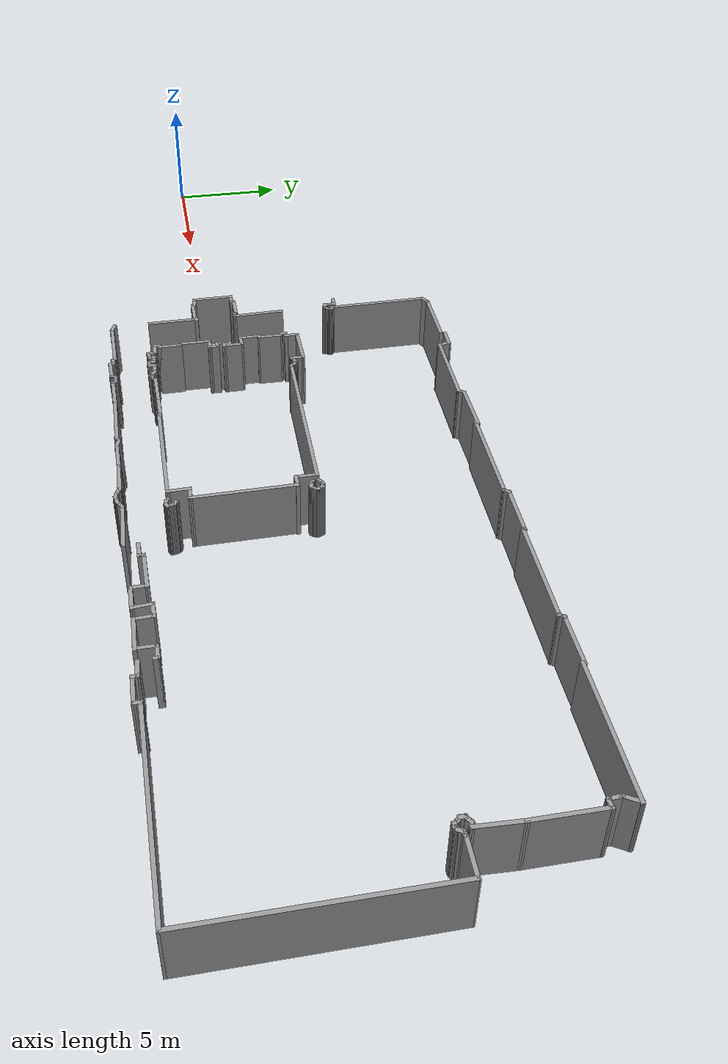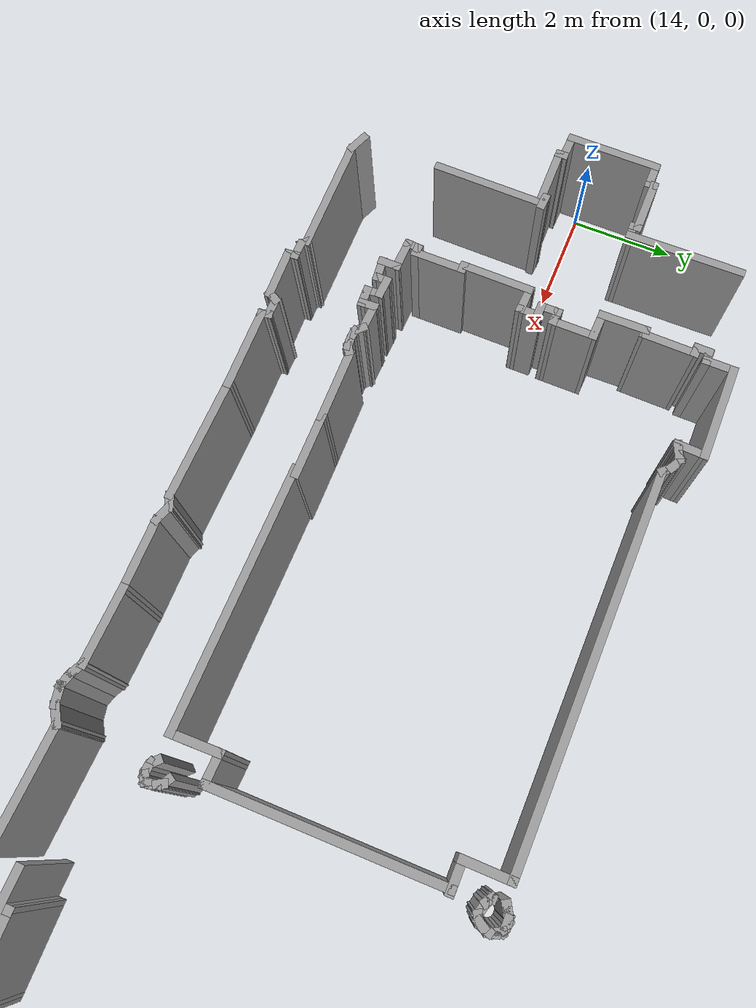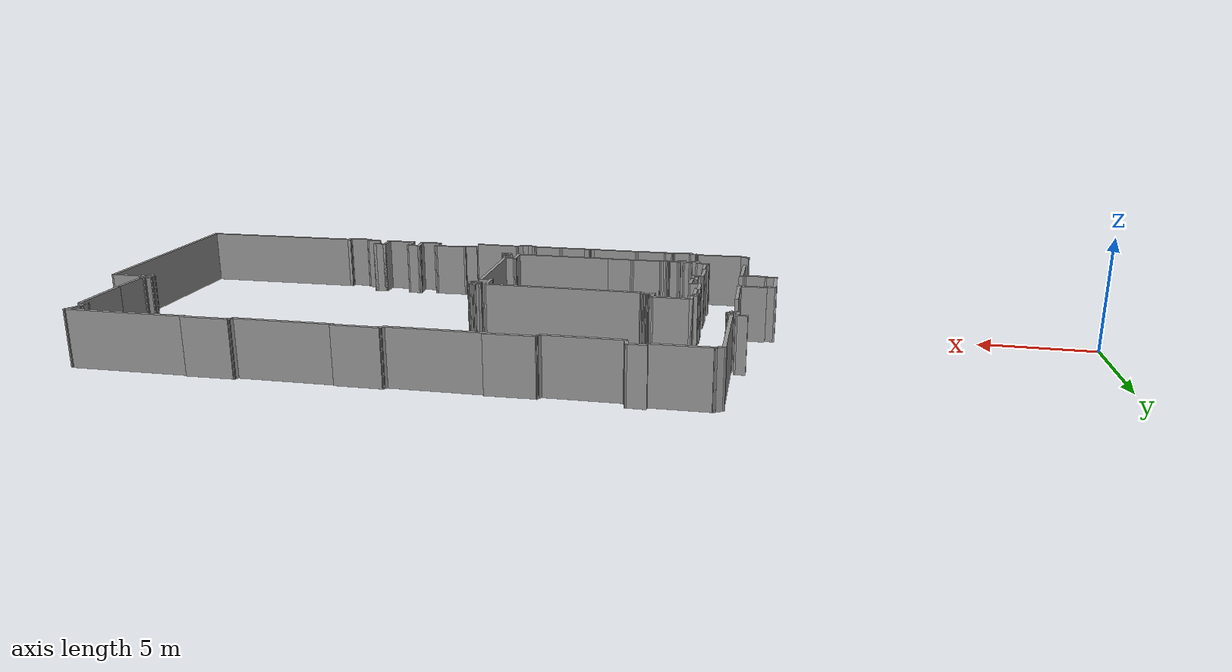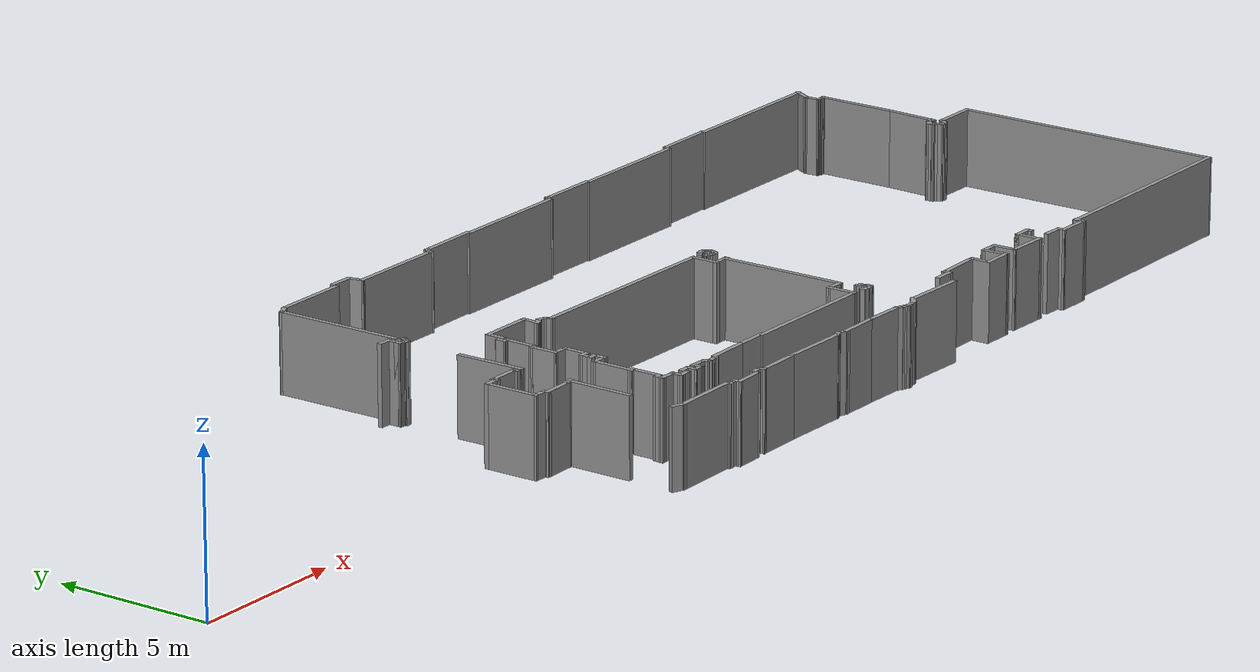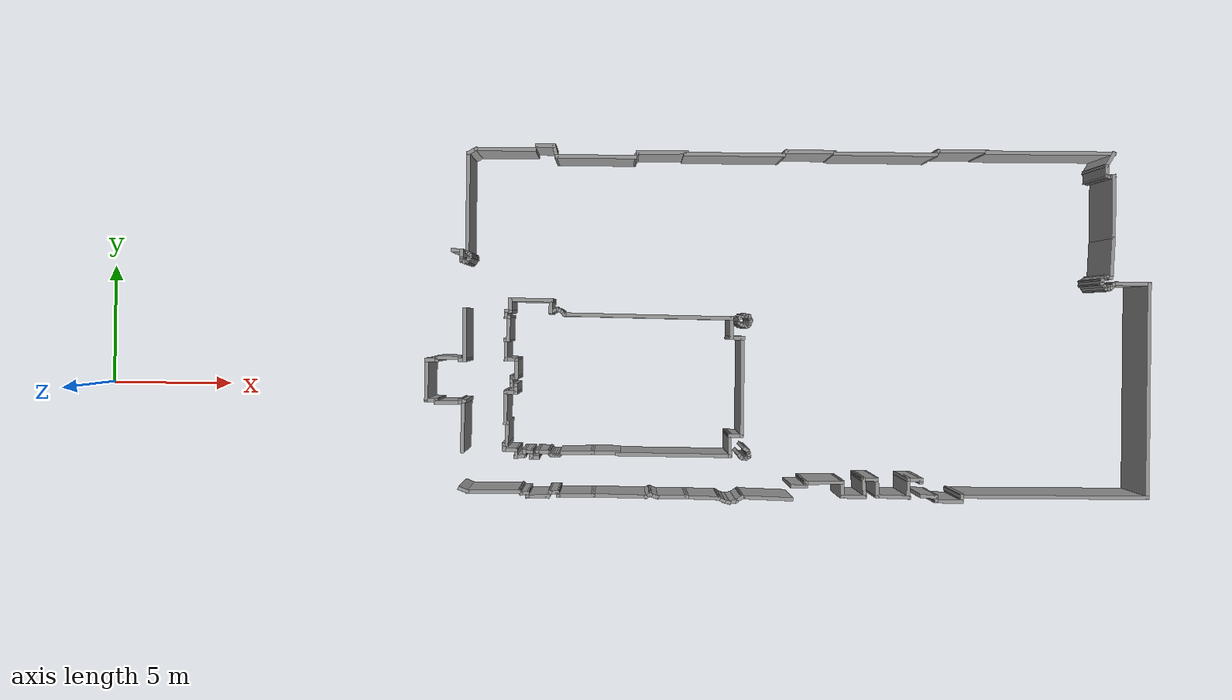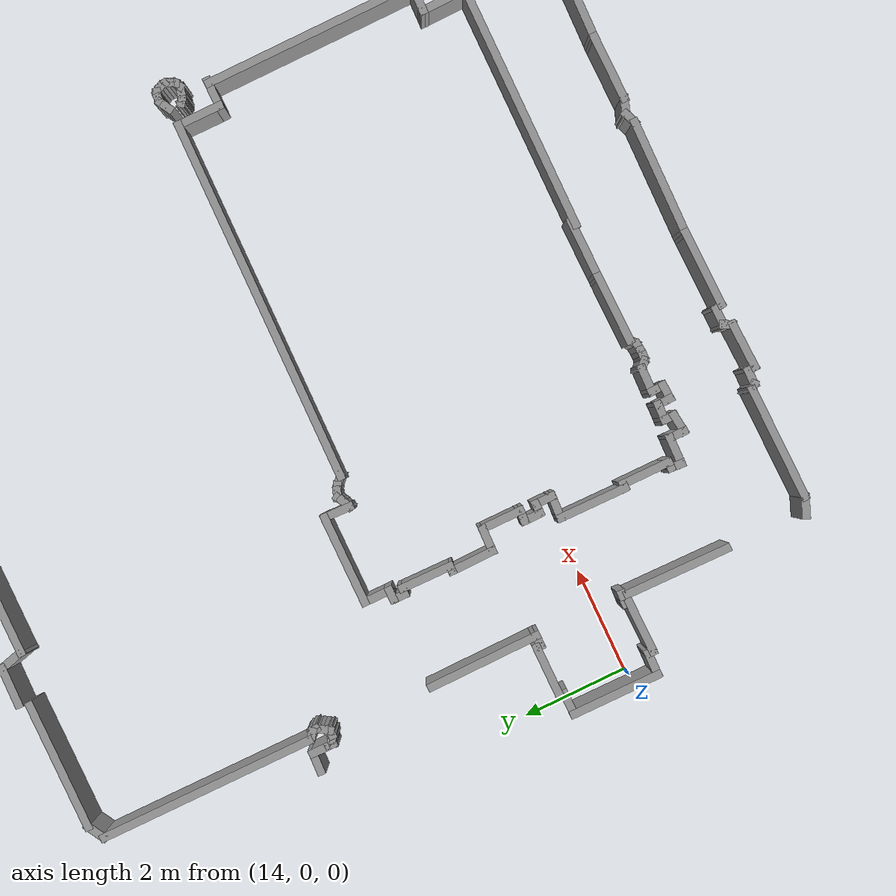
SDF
<?xml version='1.0'?>
<sdf version='1.4'>
  <model name='3_e'>
    <pose frame=''>28.6843 2.78166 0 0 -0 0</pose>
    <link name='Wall_0'>
      <collision name='Wall_0_Collision'>
        <geometry>
          <box>
            <size>2.23163 0.15 2.5</size>
          </box>
        </geometry>
        <pose frame=''>0 0 1.25 0 -0 0</pose>
      </collision>
      <visual name='Wall_0_Visual'>
        <pose frame=''>0 0 1.25 0 -0 0</pose>
        <geometry>
          <box>
            <size>2.23163 0.15 2.5</size>
          </box>
        </geometry>
        <material>
          <script>
            <uri>file://media/materials/scripts/gazebo.material</uri>
            <name>Gazebo/Grey</name>
          </script>
          <ambient>1 1 1 1</ambient>
        </material>
      </visual>
      <pose frame=''>-13.3205 -0.529565 0 0 0 -1.55975</pose>
    </link>
    <link name='Wall_1'>
      <collision name='Wall_1_Collision'>
        <geometry>
          <box>
            <size>0.3455 0.15 2.5</size>
          </box>
        </geometry>
        <pose frame=''>0 0 1.25 0 -0 0</pose>
      </collision>
      <visual name='Wall_1_Visual'>
        <pose frame=''>0 0 1.25 0 -0 0</pose>
        <geometry>
          <box>
            <size>0.3455 0.15 2.5</size>
          </box>
        </geometry>
        <material>
          <script>
            <uri>file://media/materials/scripts/gazebo.material</uri>
            <name>Gazebo/Grey</name>
          </script>
          <ambient>1 1 1 1</ambient>
        </material>
      </visual>
      <pose frame=''>-13.4067 -1.57031 0 0 -0 3.14159</pose>
    </link>
    <link name='Wall_10'>
      <collision name='Wall_10_Collision'>
        <geometry>
          <box>
            <size>1.12757 0.15 2.5</size>
          </box>
        </geometry>
        <pose frame=''>0 0 1.25 0 -0 0</pose>
      </collision>
      <visual name='Wall_10_Visual'>
        <pose frame=''>0 0 1.25 0 -0 0</pose>
        <geometry>
          <box>
            <size>1.12757 0.15 2.5</size>
          </box>
        </geometry>
        <material>
          <script>
            <uri>file://media/materials/scripts/gazebo.material</uri>
            <name>Gazebo/Grey</name>
          </script>
          <ambient>1 1 1 1</ambient>
        </material>
      </visual>
      <pose frame=''>-13.9645 -3.3328 0 0 -0 0.011764</pose>
    </link>
    <link name='Wall_100'>
      <collision name='Wall_100_Collision'>
        <geometry>
          <box>
            <size>1.07773 0.15 2.5</size>
          </box>
        </geometry>
        <pose frame=''>0 0 1.25 0 -0 0</pose>
      </collision>
      <visual name='Wall_100_Visual'>
        <pose frame=''>0 0 1.25 0 -0 0</pose>
        <geometry>
          <box>
            <size>1.07773 0.15 2.5</size>
          </box>
        </geometry>
        <material>
          <script>
            <uri>file://media/materials/scripts/gazebo.material</uri>
            <name>Gazebo/Grey</name>
          </script>
          <ambient>1 1 1 1</ambient>
        </material>
      </visual>
      <pose frame=''>2.77623 -6.99337 0 0 -0 0</pose>
    </link>
    <link name='Wall_101'>
      <collision name='Wall_101_Collision'>
        <geometry>
          <box>
            <size>0.867395 0.15 2.5</size>
          </box>
        </geometry>
        <pose frame=''>0 0 1.25 0 -0 0</pose>
      </collision>
      <visual name='Wall_101_Visual'>
        <pose frame=''>0 0 1.25 0 -0 0</pose>
        <geometry>
          <box>
            <size>0.867395 0.15 2.5</size>
          </box>
        </geometry>
        <material>
          <script>
            <uri>file://media/materials/scripts/gazebo.material</uri>
            <name>Gazebo/Grey</name>
          </script>
          <ambient>1 1 1 1</ambient>
        </material>
      </visual>
      <pose frame=''>3.20967 -6.63596 0 0 -0 1.6557</pose>
    </link>
    <link name='Wall_102'>
      <collision name='Wall_102_Collision'>
        <geometry>
          <box>
            <size>0.697515 0.15 2.5</size>
          </box>
        </geometry>
        <pose frame=''>0 0 1.25 0 -0 0</pose>
      </collision>
      <visual name='Wall_102_Visual'>
        <pose frame=''>0 0 1.25 0 -0 0</pose>
        <geometry>
          <box>
            <size>0.697515 0.15 2.5</size>
          </box>
        </geometry>
        <material>
          <script>
            <uri>file://media/materials/scripts/gazebo.material</uri>
            <name>Gazebo/Grey</name>
          </script>
          <ambient>1 1 1 1</ambient>
        </material>
      </visual>
      <pose frame=''>3.45301 -6.27856 0 0 -0 0</pose>
    </link>
    <link name='Wall_103'>
      <collision name='Wall_103_Collision'>
        <geometry>
          <box>
            <size>0.835069 0.15 2.5</size>
          </box>
        </geometry>
        <pose frame=''>0 0 1.25 0 -0 0</pose>
      </collision>
      <visual name='Wall_103_Visual'>
        <pose frame=''>0 0 1.25 0 -0 0</pose>
        <geometry>
          <box>
            <size>0.835069 0.15 2.5</size>
          </box>
        </geometry>
        <material>
          <script>
            <uri>file://media/materials/scripts/gazebo.material</uri>
            <name>Gazebo/Grey</name>
          </script>
          <ambient>1 1 1 1</ambient>
        </material>
      </visual>
      <pose frame=''>3.74198 -6.62076 0 0 0 -1.52638</pose>
    </link>
    <link name='Wall_104'>
      <collision name='Wall_104_Collision'>
        <geometry>
          <box>
            <size>1.45831 0.15 2.5</size>
          </box>
        </geometry>
        <pose frame=''>0 0 1.25 0 -0 0</pose>
      </collision>
      <visual name='Wall_104_Visual'>
        <pose frame=''>0 0 1.25 0 -0 0</pose>
        <geometry>
          <box>
            <size>1.45831 0.15 2.5</size>
          </box>
        </geometry>
        <material>
          <script>
            <uri>file://media/materials/scripts/gazebo.material</uri>
            <name>Gazebo/Grey</name>
          </script>
          <ambient>1 1 1 1</ambient>
        </material>
      </visual>
      <pose frame=''>4.41117 -6.97816 0 0 0 -0.023252</pose>
    </link>
    <link name='Wall_106'>
      <collision name='Wall_106_Collision'>
        <geometry>
          <box>
            <size>0.88002 0.15 2.5</size>
          </box>
        </geometry>
        <pose frame=''>0 0 1.25 0 -0 0</pose>
      </collision>
      <visual name='Wall_106_Visual'>
        <pose frame=''>0 0 1.25 0 -0 0</pose>
        <geometry>
          <box>
            <size>0.88002 0.15 2.5</size>
          </box>
        </geometry>
        <material>
          <script>
            <uri>file://media/materials/scripts/gazebo.material</uri>
            <name>Gazebo/Grey</name>
          </script>
          <ambient>1 1 1 1</ambient>
        </material>
      </visual>
      <pose frame=''>5.03472 -6.62836 0 0 -0 1.5708</pose>
    </link>
    <link name='Wall_107'>
      <collision name='Wall_107_Collision'>
        <geometry>
          <box>
            <size>0.667097 0.15 2.5</size>
          </box>
        </geometry>
        <pose frame=''>0 0 1.25 0 -0 0</pose>
      </collision>
      <visual name='Wall_107_Visual'>
        <pose frame=''>0 0 1.25 0 -0 0</pose>
        <geometry>
          <box>
            <size>0.667097 0.15 2.5</size>
          </box>
        </geometry>
        <material>
          <script>
            <uri>file://media/materials/scripts/gazebo.material</uri>
            <name>Gazebo/Grey</name>
          </script>
          <ambient>1 1 1 1</ambient>
        </material>
      </visual>
      <pose frame=''>5.29327 -6.26335 0 0 -0 0</pose>
    </link>
    <link name='Wall_108'>
      <collision name='Wall_108_Collision'>
        <geometry>
          <box>
            <size>0.25 0.15 2.5</size>
          </box>
        </geometry>
        <pose frame=''>0 0 1.25 0 -0 0</pose>
      </collision>
      <visual name='Wall_108_Visual'>
        <pose frame=''>0 0 1.25 0 -0 0</pose>
        <geometry>
          <box>
            <size>0.25 0.15 2.5</size>
          </box>
        </geometry>
        <material>
          <script>
            <uri>file://media/materials/scripts/gazebo.material</uri>
            <name>Gazebo/Grey</name>
          </script>
          <ambient>1 1 1 1</ambient>
        </material>
      </visual>
      <pose frame=''>5.55182 -6.31335 0 0 0 -1.5708</pose>
    </link>
    <link name='Wall_11'>
      <collision name='Wall_11_Collision'>
        <geometry>
          <box>
            <size>0.219 0.15 2.5</size>
          </box>
        </geometry>
        <pose frame=''>0 0 1.25 0 -0 0</pose>
      </collision>
      <visual name='Wall_11_Visual'>
        <pose frame=''>0 0 1.25 0 -0 0</pose>
        <geometry>
          <box>
            <size>0.219 0.15 2.5</size>
          </box>
        </geometry>
        <material>
          <script>
            <uri>file://media/materials/scripts/gazebo.material</uri>
            <name>Gazebo/Grey</name>
          </script>
          <ambient>1 1 1 1</ambient>
        </material>
      </visual>
      <pose frame=''>-13.4758 -3.29255 0 0 -0 1.5708</pose>
    </link>
    <link name='Wall_110'>
      <collision name='Wall_110_Collision'>
        <geometry>
          <box>
            <size>0.728732 0.15 2.5</size>
          </box>
        </geometry>
        <pose frame=''>0 0 1.25 0 -0 0</pose>
      </collision>
      <visual name='Wall_110_Visual'>
        <pose frame=''>0 0 1.25 0 -0 0</pose>
        <geometry>
          <box>
            <size>0.728732 0.15 2.5</size>
          </box>
        </geometry>
        <material>
          <script>
            <uri>file://media/materials/scripts/gazebo.material</uri>
            <name>Gazebo/Grey</name>
          </script>
          <ambient>1 1 1 1</ambient>
        </material>
      </visual>
      <pose frame=''>5.88641 -6.94774 0 0 0 -0.052583</pose>
    </link>
    <link name='Wall_111'>
      <collision name='Wall_111_Collision'>
        <geometry>
          <box>
            <size>0.317986 0.15 2.5</size>
          </box>
        </geometry>
        <pose frame=''>0 0 1.25 0 -0 0</pose>
      </collision>
      <visual name='Wall_111_Visual'>
        <pose frame=''>0 0 1.25 0 -0 0</pose>
        <geometry>
          <box>
            <size>0.317986 0.15 2.5</size>
          </box>
        </geometry>
        <material>
          <script>
            <uri>file://media/materials/scripts/gazebo.material</uri>
            <name>Gazebo/Grey</name>
          </script>
          <ambient>1 1 1 1</ambient>
        </material>
      </visual>
      <pose frame=''>6.18299 -7.0466 0 0 0 -1.48014</pose>
    </link>
    <link name='Wall_112'>
      <collision name='Wall_112_Collision'>
        <geometry>
          <box>
            <size>1.19951 0.15 2.5</size>
          </box>
        </geometry>
        <pose frame=''>0 0 1.25 0 -0 0</pose>
      </collision>
      <visual name='Wall_112_Visual'>
        <pose frame=''>0 0 1.25 0 -0 0</pose>
        <geometry>
          <box>
            <size>1.19951 0.15 2.5</size>
          </box>
        </geometry>
        <material>
          <script>
            <uri>file://media/materials/scripts/gazebo.material</uri>
            <name>Gazebo/Grey</name>
          </script>
          <ambient>1 1 1 1</ambient>
        </material>
      </visual>
      <pose frame=''>6.71529 -7.13785 0 0 0 -0.014492</pose>
    </link>
    <link name='Wall_113'>
      <collision name='Wall_113_Collision'>
        <geometry>
          <box>
            <size>0.39334 0.15 2.5</size>
          </box>
        </geometry>
        <pose frame=''>0 0 1.25 0 -0 0</pose>
      </collision>
      <visual name='Wall_113_Visual'>
        <pose frame=''>0 0 1.25 0 -0 0</pose>
        <geometry>
          <box>
            <size>0.39334 0.15 2.5</size>
          </box>
        </geometry>
        <material>
          <script>
            <uri>file://media/materials/scripts/gazebo.material</uri>
            <name>Gazebo/Grey</name>
          </script>
          <ambient>1 1 1 1</ambient>
        </material>
      </visual>
      <pose frame=''>7.23999 -7.02379 0 0 -0 1.5708</pose>
    </link>
    <link name='Wall_117'>
      <collision name='Wall_117_Collision'>
        <geometry>
          <box>
            <size>7.80038 0.15 2.5</size>
          </box>
        </geometry>
        <pose frame=''>0 0 1.25 0 -0 0</pose>
      </collision>
      <visual name='Wall_117_Visual'>
        <pose frame=''>0 0 1.25 0 -0 0</pose>
        <geometry>
          <box>
            <size>7.80038 0.15 2.5</size>
          </box>
        </geometry>
        <material>
          <script>
            <uri>file://media/materials/scripts/gazebo.material</uri>
            <name>Gazebo/Grey</name>
          </script>
          <ambient>1 1 1 1</ambient>
        </material>
      </visual>
      <pose frame=''>11.0437 -6.90568 0 0 -0 0.005964</pose>
    </link>
    <link name='Wall_119'>
      <collision name='Wall_119_Collision'>
        <geometry>
          <box>
            <size>8.94846 0.15 2.5</size>
          </box>
        </geometry>
        <pose frame=''>0 0 1.25 0 -0 0</pose>
      </collision>
      <visual name='Wall_119_Visual'>
        <pose frame=''>0 0 1.25 0 -0 0</pose>
        <geometry>
          <box>
            <size>8.94846 0.15 2.5</size>
          </box>
        </geometry>
        <material>
          <script>
            <uri>file://media/materials/scripts/gazebo.material</uri>
            <name>Gazebo/Grey</name>
          </script>
          <ambient>1 1 1 1</ambient>
        </material>
      </visual>
      <pose frame=''>14.858 -2.48364 0 0 -0 1.57324</pose>
    </link>
    <link name='Wall_12'>
      <collision name='Wall_12_Collision'>
        <geometry>
          <box>
            <size>0.334359 0.15 2.5</size>
          </box>
        </geometry>
        <pose frame=''>0 0 1.25 0 -0 0</pose>
      </collision>
      <visual name='Wall_12_Visual'>
        <pose frame=''>0 0 1.25 0 -0 0</pose>
        <geometry>
          <box>
            <size>0.334359 0.15 2.5</size>
          </box>
        </geometry>
        <material>
          <script>
            <uri>file://media/materials/scripts/gazebo.material</uri>
            <name>Gazebo/Grey</name>
          </script>
          <ambient>1 1 1 1</ambient>
        </material>
      </visual>
      <pose frame=''>-13.3838 -3.2638 0 0 0 -0.062419</pose>
    </link>
    <link name='Wall_121'>
      <collision name='Wall_121_Collision'>
        <geometry>
          <box>
            <size>1.5 0.15 2.5</size>
          </box>
        </geometry>
        <pose frame=''>0 0 1.25 0 -0 0</pose>
      </collision>
      <visual name='Wall_121_Visual'>
        <pose frame=''>0 0 1.25 0 -0 0</pose>
        <geometry>
          <box>
            <size>1.5 0.15 2.5</size>
          </box>
        </geometry>
        <material>
          <script>
            <uri>file://media/materials/scripts/gazebo.material</uri>
            <name>Gazebo/Grey</name>
          </script>
          <ambient>1 1 1 1</ambient>
        </material>
      </visual>
      <pose frame=''>14.1722 1.91559 0 0 -0 3.14159</pose>
    </link>
    <link name='Wall_122'>
      <collision name='Wall_122_Collision'>
        <geometry>
          <box>
            <size>0.274193 0.15 2.5</size>
          </box>
        </geometry>
        <pose frame=''>0 0 1.25 0 -0 0</pose>
      </collision>
      <visual name='Wall_122_Visual'>
        <pose frame=''>0 0 1.25 0 -0 0</pose>
        <geometry>
          <box>
            <size>0.274193 0.15 2.5</size>
          </box>
        </geometry>
        <material>
          <script>
            <uri>file://media/materials/scripts/gazebo.material</uri>
            <name>Gazebo/Grey</name>
          </script>
          <ambient>1 1 1 1</ambient>
        </material>
      </visual>
      <pose frame=''>13.4377 1.8981 0 0 0 -2.85607</pose>
    </link>
    <link name='Wall_123'>
      <collision name='Wall_123_Collision'>
        <geometry>
          <box>
            <size>0.315001 0.15 2.5</size>
          </box>
        </geometry>
        <pose frame=''>0 0 1.25 0 -0 0</pose>
      </collision>
      <visual name='Wall_123_Visual'>
        <pose frame=''>0 0 1.25 0 -0 0</pose>
        <geometry>
          <box>
            <size>0.315001 0.15 2.5</size>
          </box>
        </geometry>
        <material>
          <script>
            <uri>file://media/materials/scripts/gazebo.material</uri>
            <name>Gazebo/Grey</name>
          </script>
          <ambient>1 1 1 1</ambient>
        </material>
      </visual>
      <pose frame=''>13.3344 1.81065 0 0 0 -2.1294</pose>
    </link>
    <link name='Wall_124'>
      <collision name='Wall_124_Collision'>
        <geometry>
          <box>
            <size>0.251984 0.15 2.5</size>
          </box>
        </geometry>
        <pose frame=''>0 0 1.25 0 -0 0</pose>
      </collision>
      <visual name='Wall_124_Visual'>
        <pose frame=''>0 0 1.25 0 -0 0</pose>
        <geometry>
          <box>
            <size>0.251984 0.15 2.5</size>
          </box>
        </geometry>
        <material>
          <script>
            <uri>file://media/materials/scripts/gazebo.material</uri>
            <name>Gazebo/Grey</name>
          </script>
          <ambient>1 1 1 1</ambient>
        </material>
      </visual>
      <pose frame=''>13.2469 1.71446 0 0 0 -2.60117</pose>
    </link>
    <link name='Wall_125'>
      <collision name='Wall_125_Collision'>
        <geometry>
          <box>
            <size>0.27243 0.15 2.5</size>
          </box>
        </geometry>
        <pose frame=''>0 0 1.25 0 -0 0</pose>
      </collision>
      <visual name='Wall_125_Visual'>
        <pose frame=''>0 0 1.25 0 -0 0</pose>
        <geometry>
          <box>
            <size>0.27243 0.15 2.5</size>
          </box>
        </geometry>
        <material>
          <script>
            <uri>file://media/materials/scripts/gazebo.material</uri>
            <name>Gazebo/Grey</name>
          </script>
          <ambient>1 1 1 1</ambient>
        </material>
      </visual>
      <pose frame=''>13.142 1.68822 0 0 -0 3.14159</pose>
    </link>
    <link name='Wall_126'>
      <collision name='Wall_126_Collision'>
        <geometry>
          <box>
            <size>0.300455 0.15 2.5</size>
          </box>
        </geometry>
        <pose frame=''>0 0 1.25 0 -0 0</pose>
      </collision>
      <visual name='Wall_126_Visual'>
        <pose frame=''>0 0 1.25 0 -0 0</pose>
        <geometry>
          <box>
            <size>0.300455 0.15 2.5</size>
          </box>
        </geometry>
        <material>
          <script>
            <uri>file://media/materials/scripts/gazebo.material</uri>
            <name>Gazebo/Grey</name>
          </script>
          <ambient>1 1 1 1</ambient>
        </material>
      </visual>
      <pose frame=''>13.037 1.74944 0 0 -0 2.19105</pose>
    </link>
    <link name='Wall_127'>
      <collision name='Wall_127_Collision'>
        <geometry>
          <box>
            <size>0.273673 0.15 2.5</size>
          </box>
        </geometry>
        <pose frame=''>0 0 1.25 0 -0 0</pose>
      </collision>
      <visual name='Wall_127_Visual'>
        <pose frame=''>0 0 1.25 0 -0 0</pose>
        <geometry>
          <box>
            <size>0.273673 0.15 2.5</size>
          </box>
        </geometry>
        <material>
          <script>
            <uri>file://media/materials/scripts/gazebo.material</uri>
            <name>Gazebo/Grey</name>
          </script>
          <ambient>1 1 1 1</ambient>
        </material>
      </visual>
      <pose frame=''>12.9496 1.85438 0 0 -0 2.35619</pose>
    </link>
    <link name='Wall_128'>
      <collision name='Wall_128_Collision'>
        <geometry>
          <box>
            <size>0.307411 0.15 2.5</size>
          </box>
        </geometry>
        <pose frame=''>0 0 1.25 0 -0 0</pose>
      </collision>
      <visual name='Wall_128_Visual'>
        <pose frame=''>0 0 1.25 0 -0 0</pose>
        <geometry>
          <box>
            <size>0.307411 0.15 2.5</size>
          </box>
        </geometry>
        <material>
          <script>
            <uri>file://media/materials/scripts/gazebo.material</uri>
            <name>Gazebo/Grey</name>
          </script>
          <ambient>1 1 1 1</ambient>
        </material>
      </visual>
      <pose frame=''>12.9058 1.97681 0 0 -0 1.5708</pose>
    </link>
    <link name='Wall_129'>
      <collision name='Wall_129_Collision'>
        <geometry>
          <box>
            <size>0.276123 0.15 2.5</size>
          </box>
        </geometry>
        <pose frame=''>0 0 1.25 0 -0 0</pose>
      </collision>
      <visual name='Wall_129_Visual'>
        <pose frame=''>0 0 1.25 0 -0 0</pose>
        <geometry>
          <box>
            <size>0.276123 0.15 2.5</size>
          </box>
        </geometry>
        <material>
          <script>
            <uri>file://media/materials/scripts/gazebo.material</uri>
            <name>Gazebo/Grey</name>
          </script>
          <ambient>1 1 1 1</ambient>
        </material>
      </visual>
      <pose frame=''>12.9583 2.09049 0 0 -0 0.588003</pose>
    </link>
    <link name='Wall_130'>
      <collision name='Wall_130_Collision'>
        <geometry>
          <box>
            <size>0.276123 0.15 2.5</size>
          </box>
        </geometry>
        <pose frame=''>0 0 1.25 0 -0 0</pose>
      </collision>
      <visual name='Wall_130_Visual'>
        <pose frame=''>0 0 1.25 0 -0 0</pose>
        <geometry>
          <box>
            <size>0.276123 0.15 2.5</size>
          </box>
        </geometry>
        <material>
          <script>
            <uri>file://media/materials/scripts/gazebo.material</uri>
            <name>Gazebo/Grey</name>
          </script>
          <ambient>1 1 1 1</ambient>
        </material>
      </visual>
      <pose frame=''>13.0633 2.16045 0 0 -0 0.588003</pose>
    </link>
    <link name='Wall_131'>
      <collision name='Wall_131_Collision'>
        <geometry>
          <box>
            <size>0.31125 0.15 2.5</size>
          </box>
        </geometry>
        <pose frame=''>0 0 1.25 0 -0 0</pose>
      </collision>
      <visual name='Wall_131_Visual'>
        <pose frame=''>0 0 1.25 0 -0 0</pose>
        <geometry>
          <box>
            <size>0.31125 0.15 2.5</size>
          </box>
        </geometry>
        <material>
          <script>
            <uri>file://media/materials/scripts/gazebo.material</uri>
            <name>Gazebo/Grey</name>
          </script>
          <ambient>1 1 1 1</ambient>
        </material>
      </visual>
      <pose frame=''>13.1944 2.17794 0 0 0 -0.218669</pose>
    </link>
    <link name='Wall_132'>
      <collision name='Wall_132_Collision'>
        <geometry>
          <box>
            <size>1.76061 0.15 2.5</size>
          </box>
        </geometry>
        <pose frame=''>0 0 1.25 0 -0 0</pose>
      </collision>
      <visual name='Wall_132_Visual'>
        <pose frame=''>0 0 1.25 0 -0 0</pose>
        <geometry>
          <box>
            <size>1.76061 0.15 2.5</size>
          </box>
        </geometry>
        <material>
          <script>
            <uri>file://media/materials/scripts/gazebo.material</uri>
            <name>Gazebo/Grey</name>
          </script>
          <ambient>1 1 1 1</ambient>
        </material>
      </visual>
      <pose frame=''>13.3081 2.965 0 0 -0 1.52734</pose>
    </link>
    <link name='Wall_134'>
      <collision name='Wall_134_Collision'>
        <geometry>
          <box>
            <size>2.72104 0.15 2.5</size>
          </box>
        </geometry>
        <pose frame=''>0 0 1.25 0 -0 0</pose>
      </collision>
      <visual name='Wall_134_Visual'>
        <pose frame=''>0 0 1.25 0 -0 0</pose>
        <geometry>
          <box>
            <size>2.72104 0.15 2.5</size>
          </box>
        </geometry>
        <material>
          <script>
            <uri>file://media/materials/scripts/gazebo.material</uri>
            <name>Gazebo/Grey</name>
          </script>
          <ambient>1 1 1 1</ambient>
        </material>
      </visual>
      <pose frame=''>13.3431 5.05506 0 0 -0 1.5708</pose>
    </link>
    <link name='Wall_135'>
      <collision name='Wall_135_Collision'>
        <geometry>
          <box>
            <size>0.25 0.15 2.5</size>
          </box>
        </geometry>
        <pose frame=''>0 0 1.25 0 -0 0</pose>
      </collision>
      <visual name='Wall_135_Visual'>
        <pose frame=''>0 0 1.25 0 -0 0</pose>
        <geometry>
          <box>
            <size>0.25 0.15 2.5</size>
          </box>
        </geometry>
        <material>
          <script>
            <uri>file://media/materials/scripts/gazebo.material</uri>
            <name>Gazebo/Grey</name>
          </script>
          <ambient>1 1 1 1</ambient>
        </material>
      </visual>
      <pose frame=''>13.2948 6.32764 0 0 0 -2.87979</pose>
    </link>
    <link name='Wall_136'>
      <collision name='Wall_136_Collision'>
        <geometry>
          <box>
            <size>0.25 0.15 2.5</size>
          </box>
        </geometry>
        <pose frame=''>0 0 1.25 0 -0 0</pose>
      </collision>
      <visual name='Wall_136_Visual'>
        <pose frame=''>0 0 1.25 0 -0 0</pose>
        <geometry>
          <box>
            <size>0.25 0.15 2.5</size>
          </box>
        </geometry>
        <material>
          <script>
            <uri>file://media/materials/scripts/gazebo.material</uri>
            <name>Gazebo/Grey</name>
          </script>
          <ambient>1 1 1 1</ambient>
        </material>
      </visual>
      <pose frame=''>13.1965 6.3147 0 0 -0 3.14159</pose>
    </link>
    <link name='Wall_137'>
      <collision name='Wall_137_Collision'>
        <geometry>
          <box>
            <size>0.25 0.15 2.5</size>
          </box>
        </geometry>
        <pose frame=''>0 0 1.25 0 -0 0</pose>
      </collision>
      <visual name='Wall_137_Visual'>
        <pose frame=''>0 0 1.25 0 -0 0</pose>
        <geometry>
          <box>
            <size>0.25 0.15 2.5</size>
          </box>
        </geometry>
        <material>
          <script>
            <uri>file://media/materials/scripts/gazebo.material</uri>
            <name>Gazebo/Grey</name>
          </script>
          <ambient>1 1 1 1</ambient>
        </material>
      </visual>
      <pose frame=''>13.0982 6.32764 0 0 -0 2.87979</pose>
    </link>
    <link name='Wall_138'>
      <collision name='Wall_138_Collision'>
        <geometry>
          <box>
            <size>0.15 0.15 2.5</size>
          </box>
        </geometry>
        <pose frame=''>0 0 1.25 0 -0 0</pose>
      </collision>
      <visual name='Wall_138_Visual'>
        <pose frame=''>0 0 1.25 0 -0 0</pose>
        <geometry>
          <box>
            <size>0.15 0.15 2.5</size>
          </box>
        </geometry>
        <material>
          <script>
            <uri>file://media/materials/scripts/gazebo.material</uri>
            <name>Gazebo/Grey</name>
          </script>
          <ambient>1 1 1 1</ambient>
        </material>
      </visual>
      <pose frame=''>13.0499 6.34058 0 0 -0 0</pose>
    </link>
    <link name='Wall_139'>
      <collision name='Wall_139_Collision'>
        <geometry>
          <box>
            <size>0.568581 0.15 2.5</size>
          </box>
        </geometry>
        <pose frame=''>0 0 1.25 0 -0 0</pose>
      </collision>
      <visual name='Wall_139_Visual'>
        <pose frame=''>0 0 1.25 0 -0 0</pose>
        <geometry>
          <box>
            <size>0.568581 0.15 2.5</size>
          </box>
        </geometry>
        <material>
          <script>
            <uri>file://media/materials/scripts/gazebo.material</uri>
            <name>Gazebo/Grey</name>
          </script>
          <ambient>1 1 1 1</ambient>
        </material>
      </visual>
      <pose frame=''>13.0396 6.54962 0 0 -0 1.62</pose>
    </link>
    <link name='Wall_140'>
      <collision name='Wall_140_Collision'>
        <geometry>
          <box>
            <size>0.75 0.15 2.5</size>
          </box>
        </geometry>
        <pose frame=''>0 0 1.25 0 -0 0</pose>
      </collision>
      <visual name='Wall_140_Visual'>
        <pose frame=''>0 0 1.25 0 -0 0</pose>
        <geometry>
          <box>
            <size>0.75 0.15 2.5</size>
          </box>
        </geometry>
        <material>
          <script>
            <uri>file://media/materials/scripts/gazebo.material</uri>
            <name>Gazebo/Grey</name>
          </script>
          <ambient>1 1 1 1</ambient>
        </material>
      </visual>
      <pose frame=''>13.1693 7.00846 0 0 -0 1.0472</pose>
    </link>
    <link name='Wall_142'>
      <collision name='Wall_142_Collision'>
        <geometry>
          <box>
            <size>5.3732 0.15 2.5</size>
          </box>
        </geometry>
        <pose frame=''>0 0 1.25 0 -0 0</pose>
      </collision>
      <visual name='Wall_142_Visual'>
        <pose frame=''>0 0 1.25 0 -0 0</pose>
        <geometry>
          <box>
            <size>5.3732 0.15 2.5</size>
          </box>
        </geometry>
        <material>
          <script>
            <uri>file://media/materials/scripts/gazebo.material</uri>
            <name>Gazebo/Grey</name>
          </script>
          <ambient>1 1 1 1</ambient>
        </material>
      </visual>
      <pose frame=''>10.7078 7.25589 0 0 0 -3.13685</pose>
    </link>
    <link name='Wall_144'>
      <collision name='Wall_144_Collision'>
        <geometry>
          <box>
            <size>2.13953 0.15 2.5</size>
          </box>
        </geometry>
        <pose frame=''>0 0 1.25 0 -0 0</pose>
      </collision>
      <visual name='Wall_144_Visual'>
        <pose frame=''>0 0 1.25 0 -0 0</pose>
        <geometry>
          <box>
            <size>2.13953 0.15 2.5</size>
          </box>
        </geometry>
        <material>
          <script>
            <uri>file://media/materials/scripts/gazebo.material</uri>
            <name>Gazebo/Grey</name>
          </script>
          <ambient>1 1 1 1</ambient>
        </material>
      </visual>
      <pose frame=''>7.103 7.28679 0 0 -0 0.01156</pose>
    </link>
    <link name='Wall_146'>
      <collision name='Wall_146_Collision'>
        <geometry>
          <box>
            <size>4.3015 0.15 2.5</size>
          </box>
        </geometry>
        <pose frame=''>0 0 1.25 0 -0 0</pose>
      </collision>
      <visual name='Wall_146_Visual'>
        <pose frame=''>0 0 1.25 0 -0 0</pose>
        <geometry>
          <box>
            <size>4.3015 0.15 2.5</size>
          </box>
        </geometry>
        <material>
          <script>
            <uri>file://media/materials/scripts/gazebo.material</uri>
            <name>Gazebo/Grey</name>
          </script>
          <ambient>1 1 1 1</ambient>
        </material>
      </visual>
      <pose frame=''>3.9175 7.12579 0 0 -0 0</pose>
    </link>
    <link name='Wall_147'>
      <collision name='Wall_147_Collision'>
        <geometry>
          <box>
            <size>0.338614 0.15 2.5</size>
          </box>
        </geometry>
        <pose frame=''>0 0 1.25 0 -0 0</pose>
      </collision>
      <visual name='Wall_147_Visual'>
        <pose frame=''>0 0 1.25 0 -0 0</pose>
        <geometry>
          <box>
            <size>0.338614 0.15 2.5</size>
          </box>
        </geometry>
        <material>
          <script>
            <uri>file://media/materials/scripts/gazebo.material</uri>
            <name>Gazebo/Grey</name>
          </script>
          <ambient>1 1 1 1</ambient>
        </material>
      </visual>
      <pose frame=''>6.05075 7.20054 0 0 -0 0.915101</pose>
    </link>
    <link name='Wall_149'>
      <collision name='Wall_149_Collision'>
        <geometry>
          <box>
            <size>2.128 0.15 2.5</size>
          </box>
        </geometry>
        <pose frame=''>0 0 1.25 0 -0 0</pose>
      </collision>
      <visual name='Wall_149_Visual'>
        <pose frame=''>0 0 1.25 0 -0 0</pose>
        <geometry>
          <box>
            <size>2.128 0.15 2.5</size>
          </box>
        </geometry>
        <material>
          <script>
            <uri>file://media/materials/scripts/gazebo.material</uri>
            <name>Gazebo/Grey</name>
          </script>
          <ambient>1 1 1 1</ambient>
        </material>
      </visual>
      <pose frame=''>0.829752 7.18329 0 0 -0 0</pose>
    </link>
    <link name='Wall_151'>
      <collision name='Wall_151_Collision'>
        <geometry>
          <box>
            <size>4.1865 0.15 2.5</size>
          </box>
        </geometry>
        <pose frame=''>0 0 1.25 0 -0 0</pose>
      </collision>
      <visual name='Wall_151_Visual'>
        <pose frame=''>0 0 1.25 0 -0 0</pose>
        <geometry>
          <box>
            <size>4.1865 0.15 2.5</size>
          </box>
        </geometry>
        <material>
          <script>
            <uri>file://media/materials/scripts/gazebo.material</uri>
            <name>Gazebo/Grey</name>
          </script>
          <ambient>1 1 1 1</ambient>
        </material>
      </visual>
      <pose frame=''>-2.2925 7.03379 0 0 -0 0</pose>
    </link>
    <link name='Wall_152'>
      <collision name='Wall_152_Collision'>
        <geometry>
          <box>
            <size>0.338614 0.15 2.5</size>
          </box>
        </geometry>
        <pose frame=''>0 0 1.25 0 -0 0</pose>
      </collision>
      <visual name='Wall_152_Visual'>
        <pose frame=''>0 0 1.25 0 -0 0</pose>
        <geometry>
          <box>
            <size>0.338614 0.15 2.5</size>
          </box>
        </geometry>
        <material>
          <script>
            <uri>file://media/materials/scripts/gazebo.material</uri>
            <name>Gazebo/Grey</name>
          </script>
          <ambient>1 1 1 1</ambient>
        </material>
      </visual>
      <pose frame=''>-0.216747 7.10854 0 0 -0 0.915101</pose>
    </link>
    <link name='Wall_154'>
      <collision name='Wall_154_Collision'>
        <geometry>
          <box>
            <size>2.16263 0.15 2.5</size>
          </box>
        </geometry>
        <pose frame=''>0 0 1.25 0 -0 0</pose>
      </collision>
      <visual name='Wall_154_Visual'>
        <pose frame=''>0 0 1.25 0 -0 0</pose>
        <geometry>
          <box>
            <size>2.16263 0.15 2.5</size>
          </box>
        </geometry>
        <material>
          <script>
            <uri>file://media/materials/scripts/gazebo.material</uri>
            <name>Gazebo/Grey</name>
          </script>
          <ambient>1 1 1 1</ambient>
        </material>
      </visual>
      <pose frame=''>-5.271 7.08554 0 0 -0 0.017141</pose>
    </link>
    <link name='Wall_156'>
      <collision name='Wall_156_Collision'>
        <geometry>
          <box>
            <size>3.37008 0.15 2.5</size>
          </box>
        </geometry>
        <pose frame=''>0 0 1.25 0 -0 0</pose>
      </collision>
      <visual name='Wall_156_Visual'>
        <pose frame=''>0 0 1.25 0 -0 0</pose>
        <geometry>
          <box>
            <size>3.37008 0.15 2.5</size>
          </box>
        </geometry>
        <material>
          <script>
            <uri>file://media/materials/scripts/gazebo.material</uri>
            <name>Gazebo/Grey</name>
          </script>
          <ambient>1 1 1 1</ambient>
        </material>
      </visual>
      <pose frame=''>-8.01375 6.87279 0 0 -0 0</pose>
    </link>
    <link name='Wall_157'>
      <collision name='Wall_157_Collision'>
        <geometry>
          <box>
            <size>0.382857 0.15 2.5</size>
          </box>
        </geometry>
        <pose frame=''>0 0 1.25 0 -0 0</pose>
      </collision>
      <visual name='Wall_157_Visual'>
        <pose frame=''>0 0 1.25 0 -0 0</pose>
        <geometry>
          <box>
            <size>0.382857 0.15 2.5</size>
          </box>
        </geometry>
        <material>
          <script>
            <uri>file://media/materials/scripts/gazebo.material</uri>
            <name>Gazebo/Grey</name>
          </script>
          <ambient>1 1 1 1</ambient>
        </material>
      </visual>
      <pose frame=''>-6.3405 6.97054 0 0 -0 0.996491</pose>
    </link>
    <link name='Wall_159'>
      <collision name='Wall_159_Collision'>
        <geometry>
          <box>
            <size>2.54203 0.15 2.5</size>
          </box>
        </geometry>
        <pose frame=''>0 0 1.25 0 -0 0</pose>
      </collision>
      <visual name='Wall_159_Visual'>
        <pose frame=''>0 0 1.25 0 -0 0</pose>
        <geometry>
          <box>
            <size>2.54203 0.15 2.5</size>
          </box>
        </geometry>
        <material>
          <script>
            <uri>file://media/materials/scripts/gazebo.material</uri>
            <name>Gazebo/Grey</name>
          </script>
          <ambient>1 1 1 1</ambient>
        </material>
      </visual>
      <pose frame=''>-11.7512 7.13154 0 0 -0 0.004808</pose>
    </link>
    <link name='Wall_16'>
      <collision name='Wall_16_Collision'>
        <geometry>
          <box>
            <size>2.10098 0.15 2.5</size>
          </box>
        </geometry>
        <pose frame=''>0 0 1.25 0 -0 0</pose>
      </collision>
      <visual name='Wall_16_Visual'>
        <pose frame=''>0 0 1.25 0 -0 0</pose>
        <geometry>
          <box>
            <size>2.10098 0.15 2.5</size>
          </box>
        </geometry>
        <material>
          <script>
            <uri>file://media/materials/scripts/gazebo.material</uri>
            <name>Gazebo/Grey</name>
          </script>
          <ambient>1 1 1 1</ambient>
        </material>
      </visual>
      <pose frame=''>-13.3491 -4.3434 0 0 0 -1.58242</pose>
    </link>
    <link name='Wall_162'>
      <collision name='Wall_162_Collision'>
        <geometry>
          <box>
            <size>0.851594 0.15 2.5</size>
          </box>
        </geometry>
        <pose frame=''>0 0 1.25 0 -0 0</pose>
      </collision>
      <visual name='Wall_162_Visual'>
        <pose frame=''>0 0 1.25 0 -0 0</pose>
        <geometry>
          <box>
            <size>0.851594 0.15 2.5</size>
          </box>
        </geometry>
        <material>
          <script>
            <uri>file://media/materials/scripts/gazebo.material</uri>
            <name>Gazebo/Grey</name>
          </script>
          <ambient>1 1 1 1</ambient>
        </material>
      </visual>
      <pose frame=''>-10.0895 7.30404 0 0 0 -0.016392</pose>
    </link>
    <link name='Wall_163'>
      <collision name='Wall_163_Collision'>
        <geometry>
          <box>
            <size>0.590767 0.15 2.5</size>
          </box>
        </geometry>
        <pose frame=''>0 0 1.25 0 -0 0</pose>
      </collision>
      <visual name='Wall_163_Visual'>
        <pose frame=''>0 0 1.25 0 -0 0</pose>
        <geometry>
          <box>
            <size>0.590767 0.15 2.5</size>
          </box>
        </geometry>
        <material>
          <script>
            <uri>file://media/materials/scripts/gazebo.material</uri>
            <name>Gazebo/Grey</name>
          </script>
          <ambient>1 1 1 1</ambient>
        </material>
      </visual>
      <pose frame=''>-9.68125 7.08554 0 0 0 -1.30683</pose>
    </link>
    <link name='Wall_165'>
      <collision name='Wall_165_Collision'>
        <geometry>
          <box>
            <size>0.5 0.15 2.5</size>
          </box>
        </geometry>
        <pose frame=''>0 0 1.25 0 -0 0</pose>
      </collision>
      <visual name='Wall_165_Visual'>
        <pose frame=''>0 0 1.25 0 -0 0</pose>
        <geometry>
          <box>
            <size>0.5 0.15 2.5</size>
          </box>
        </geometry>
        <material>
          <script>
            <uri>file://media/materials/scripts/gazebo.material</uri>
            <name>Gazebo/Grey</name>
          </script>
          <ambient>1 1 1 1</ambient>
        </material>
      </visual>
      <pose frame=''>-13.0988 7.03829 0 0 0 -2.61799</pose>
    </link>
    <link name='Wall_166'>
      <collision name='Wall_166_Collision'>
        <geometry>
          <box>
            <size>4.19923 0.15 2.5</size>
          </box>
        </geometry>
        <pose frame=''>0 0 1.25 0 -0 0</pose>
      </collision>
      <visual name='Wall_166_Visual'>
        <pose frame=''>0 0 1.25 0 -0 0</pose>
        <geometry>
          <box>
            <size>4.19923 0.15 2.5</size>
          </box>
        </geometry>
        <material>
          <script>
            <uri>file://media/materials/scripts/gazebo.material</uri>
            <name>Gazebo/Grey</name>
          </script>
          <ambient>1 1 1 1</ambient>
        </material>
      </visual>
      <pose frame=''>-13.2511 4.92618 0 0 0 -1.57115</pose>
    </link>
    <link name='Wall_168'>
      <collision name='Wall_168_Collision'>
        <geometry>
          <box>
            <size>0.28225 0.15 2.5</size>
          </box>
        </geometry>
        <pose frame=''>0 0 1.25 0 -0 0</pose>
      </collision>
      <visual name='Wall_168_Visual'>
        <pose frame=''>0 0 1.25 0 -0 0</pose>
        <geometry>
          <box>
            <size>0.28225 0.15 2.5</size>
          </box>
        </geometry>
        <material>
          <script>
            <uri>file://media/materials/scripts/gazebo.material</uri>
            <name>Gazebo/Grey</name>
          </script>
          <ambient>1 1 1 1</ambient>
        </material>
      </visual>
      <pose frame=''>-13.1892 2.81404 0 0 0 -0.643501</pose>
    </link>
    <link name='Wall_169'>
      <collision name='Wall_169_Collision'>
        <geometry>
          <box>
            <size>0.230445 0.15 2.5</size>
          </box>
        </geometry>
        <pose frame=''>0 0 1.25 0 -0 0</pose>
      </collision>
      <visual name='Wall_169_Visual'>
        <pose frame=''>0 0 1.25 0 -0 0</pose>
        <geometry>
          <box>
            <size>0.230445 0.15 2.5</size>
          </box>
        </geometry>
        <material>
          <script>
            <uri>file://media/materials/scripts/gazebo.material</uri>
            <name>Gazebo/Grey</name>
          </script>
          <ambient>1 1 1 1</ambient>
        </material>
      </visual>
      <pose frame=''>-13.1297 2.73469 0 0 0 -1.40565</pose>
    </link>
    <link name='Wall_170'>
      <collision name='Wall_170_Collision'>
        <geometry>
          <box>
            <size>0.28616 0.15 2.5</size>
          </box>
        </geometry>
        <pose frame=''>0 0 1.25 0 -0 0</pose>
      </collision>
      <visual name='Wall_170_Visual'>
        <pose frame=''>0 0 1.25 0 -0 0</pose>
        <geometry>
          <box>
            <size>0.28616 0.15 2.5</size>
          </box>
        </geometry>
        <material>
          <script>
            <uri>file://media/materials/scripts/gazebo.material</uri>
            <name>Gazebo/Grey</name>
          </script>
          <ambient>1 1 1 1</ambient>
        </material>
      </visual>
      <pose frame=''>-13.1561 2.63551 0 0 0 -2.07789</pose>
    </link>
    <link name='Wall_171'>
      <collision name='Wall_171_Collision'>
        <geometry>
          <box>
            <size>0.263766 0.15 2.5</size>
          </box>
        </geometry>
        <pose frame=''>0 0 1.25 0 -0 0</pose>
      </collision>
      <visual name='Wall_171_Visual'>
        <pose frame=''>0 0 1.25 0 -0 0</pose>
        <geometry>
          <box>
            <size>0.263766 0.15 2.5</size>
          </box>
        </geometry>
        <material>
          <script>
            <uri>file://media/materials/scripts/gazebo.material</uri>
            <name>Gazebo/Grey</name>
          </script>
          <ambient>1 1 1 1</ambient>
        </material>
      </visual>
      <pose frame=''>-13.2223 2.52971 0 0 0 -2.19105</pose>
    </link>
    <link name='Wall_172'>
      <collision name='Wall_172_Collision'>
        <geometry>
          <box>
            <size>0.242575 0.15 2.5</size>
          </box>
        </geometry>
        <pose frame=''>0 0 1.25 0 -0 0</pose>
      </collision>
      <visual name='Wall_172_Visual'>
        <pose frame=''>0 0 1.25 0 -0 0</pose>
        <geometry>
          <box>
            <size>0.242575 0.15 2.5</size>
          </box>
        </geometry>
        <material>
          <script>
            <uri>file://media/materials/scripts/gazebo.material</uri>
            <name>Gazebo/Grey</name>
          </script>
          <ambient>1 1 1 1</ambient>
        </material>
      </visual>
      <pose frame=''>-13.3016 2.48342 0 0 -0 3.14159</pose>
    </link>
    <link name='Wall_173'>
      <collision name='Wall_173_Collision'>
        <geometry>
          <box>
            <size>0.227114 0.15 2.5</size>
          </box>
        </geometry>
        <pose frame=''>0 0 1.25 0 -0 0</pose>
      </collision>
      <visual name='Wall_173_Visual'>
        <pose frame=''>0 0 1.25 0 -0 0</pose>
        <geometry>
          <box>
            <size>0.227114 0.15 2.5</size>
          </box>
        </geometry>
        <material>
          <script>
            <uri>file://media/materials/scripts/gazebo.material</uri>
            <name>Gazebo/Grey</name>
          </script>
          <ambient>1 1 1 1</ambient>
        </material>
      </visual>
      <pose frame=''>-13.381 2.50325 0 0 -0 2.60117</pose>
    </link>
    <link name='Wall_174'>
      <collision name='Wall_174_Collision'>
        <geometry>
          <box>
            <size>0.230445 0.15 2.5</size>
          </box>
        </geometry>
        <pose frame=''>0 0 1.25 0 -0 0</pose>
      </collision>
      <visual name='Wall_174_Visual'>
        <pose frame=''>0 0 1.25 0 -0 0</pose>
        <geometry>
          <box>
            <size>0.230445 0.15 2.5</size>
          </box>
        </geometry>
        <material>
          <script>
            <uri>file://media/materials/scripts/gazebo.material</uri>
            <name>Gazebo/Grey</name>
          </script>
          <ambient>1 1 1 1</ambient>
        </material>
      </visual>
      <pose frame=''>-13.4537 2.52971 0 0 -0 2.97644</pose>
    </link>
    <link name='Wall_175'>
      <collision name='Wall_175_Collision'>
        <geometry>
          <box>
            <size>0.22935 0.15 2.5</size>
          </box>
        </geometry>
        <pose frame=''>0 0 1.25 0 -0 0</pose>
      </collision>
      <visual name='Wall_175_Visual'>
        <pose frame=''>0 0 1.25 0 -0 0</pose>
        <geometry>
          <box>
            <size>0.22935 0.15 2.5</size>
          </box>
        </geometry>
        <material>
          <script>
            <uri>file://media/materials/scripts/gazebo.material</uri>
            <name>Gazebo/Grey</name>
          </script>
          <ambient>1 1 1 1</ambient>
        </material>
      </visual>
      <pose frame=''>-13.4934 2.57599 0 0 -0 1.5708</pose>
    </link>
    <link name='Wall_176'>
      <collision name='Wall_176_Collision'>
        <geometry>
          <box>
            <size>0.4674 0.15 2.5</size>
          </box>
        </geometry>
        <pose frame=''>0 0 1.25 0 -0 0</pose>
      </collision>
      <visual name='Wall_176_Visual'>
        <pose frame=''>0 0 1.25 0 -0 0</pose>
        <geometry>
          <box>
            <size>0.4674 0.15 2.5</size>
          </box>
        </geometry>
        <material>
          <script>
            <uri>file://media/materials/scripts/gazebo.material</uri>
            <name>Gazebo/Grey</name>
          </script>
          <ambient>1 1 1 1</ambient>
        </material>
      </visual>
      <pose frame=''>-13.4934 2.77437 0 0 -0 1.5708</pose>
    </link>
    <link name='Wall_177'>
      <collision name='Wall_177_Collision'>
        <geometry>
          <box>
            <size>0.494104 0.15 2.5</size>
          </box>
        </geometry>
        <pose frame=''>0 0 1.25 0 -0 0</pose>
      </collision>
      <visual name='Wall_177_Visual'>
        <pose frame=''>0 0 1.25 0 -0 0</pose>
        <geometry>
          <box>
            <size>0.494104 0.15 2.5</size>
          </box>
        </geometry>
        <material>
          <script>
            <uri>file://media/materials/scripts/gazebo.material</uri>
            <name>Gazebo/Grey</name>
          </script>
          <ambient>1 1 1 1</ambient>
        </material>
      </visual>
      <pose frame=''>-13.6653 2.93968 0 0 -0 3.10315</pose>
    </link>
    <link name='Wall_179'>
      <collision name='Wall_179_Collision'>
        <geometry>
          <box>
            <size>0.25 0.15 2.5</size>
          </box>
        </geometry>
        <pose frame=''>0 0 1.25 0 -0 0</pose>
      </collision>
      <visual name='Wall_179_Visual'>
        <pose frame=''>0 0 1.25 0 -0 0</pose>
        <geometry>
          <box>
            <size>0.25 0.15 2.5</size>
          </box>
        </geometry>
        <material>
          <script>
            <uri>file://media/materials/scripts/gazebo.material</uri>
            <name>Gazebo/Grey</name>
          </script>
          <ambient>1 1 1 1</ambient>
        </material>
      </visual>
      <pose frame=''>-1.94886 0.330471 0 0 -0 0.523599</pose>
    </link>
    <link name='Wall_18'>
      <collision name='Wall_18_Collision'>
        <geometry>
          <box>
            <size>0.317296 0.15 2.5</size>
          </box>
        </geometry>
        <pose frame=''>0 0 1.25 0 -0 0</pose>
      </collision>
      <visual name='Wall_18_Visual'>
        <pose frame=''>0 0 1.25 0 -0 0</pose>
        <geometry>
          <box>
            <size>0.317296 0.15 2.5</size>
          </box>
        </geometry>
        <material>
          <script>
            <uri>file://media/materials/scripts/gazebo.material</uri>
            <name>Gazebo/Grey</name>
          </script>
          <ambient>1 1 1 1</ambient>
        </material>
      </visual>
      <pose frame=''>-11.5341 0.452297 0 0 -0 0</pose>
    </link>
    <link name='Wall_180'>
      <collision name='Wall_180_Collision'>
        <geometry>
          <box>
            <size>0.25 0.15 2.5</size>
          </box>
        </geometry>
        <pose frame=''>0 0 1.25 0 -0 0</pose>
      </collision>
      <visual name='Wall_180_Visual'>
        <pose frame=''>0 0 1.25 0 -0 0</pose>
        <geometry>
          <box>
            <size>0.25 0.15 2.5</size>
          </box>
        </geometry>
        <material>
          <script>
            <uri>file://media/materials/scripts/gazebo.material</uri>
            <name>Gazebo/Grey</name>
          </script>
          <ambient>1 1 1 1</ambient>
        </material>
      </visual>
      <pose frame=''>-1.86226 0.380471 0 0 -0 0.523599</pose>
    </link>
    <link name='Wall_181'>
      <collision name='Wall_181_Collision'>
        <geometry>
          <box>
            <size>0.25 0.15 2.5</size>
          </box>
        </geometry>
        <pose frame=''>0 0 1.25 0 -0 0</pose>
      </collision>
      <visual name='Wall_181_Visual'>
        <pose frame=''>0 0 1.25 0 -0 0</pose>
        <geometry>
          <box>
            <size>0.25 0.15 2.5</size>
          </box>
        </geometry>
        <material>
          <script>
            <uri>file://media/materials/scripts/gazebo.material</uri>
            <name>Gazebo/Grey</name>
          </script>
          <ambient>1 1 1 1</ambient>
        </material>
      </visual>
      <pose frame=''>-1.76896 0.405471 0 0 -0 0</pose>
    </link>
    <link name='Wall_182'>
      <collision name='Wall_182_Collision'>
        <geometry>
          <box>
            <size>0.25 0.15 2.5</size>
          </box>
        </geometry>
        <pose frame=''>0 0 1.25 0 -0 0</pose>
      </collision>
      <visual name='Wall_182_Visual'>
        <pose frame=''>0 0 1.25 0 -0 0</pose>
        <geometry>
          <box>
            <size>0.25 0.15 2.5</size>
          </box>
        </geometry>
        <material>
          <script>
            <uri>file://media/materials/scripts/gazebo.material</uri>
            <name>Gazebo/Grey</name>
          </script>
          <ambient>1 1 1 1</ambient>
        </material>
      </visual>
      <pose frame=''>-1.67066 0.39253 0 0 0 -0.261799</pose>
    </link>
    <link name='Wall_183'>
      <collision name='Wall_183_Collision'>
        <geometry>
          <box>
            <size>0.25 0.15 2.5</size>
          </box>
        </geometry>
        <pose frame=''>0 0 1.25 0 -0 0</pose>
      </collision>
      <visual name='Wall_183_Visual'>
        <pose frame=''>0 0 1.25 0 -0 0</pose>
        <geometry>
          <box>
            <size>0.25 0.15 2.5</size>
          </box>
        </geometry>
        <material>
          <script>
            <uri>file://media/materials/scripts/gazebo.material</uri>
            <name>Gazebo/Grey</name>
          </script>
          <ambient>1 1 1 1</ambient>
        </material>
      </visual>
      <pose frame=''>-1.59736 0.336288 0 0 0 -1.0472</pose>
    </link>
    <link name='Wall_184'>
      <collision name='Wall_184_Collision'>
        <geometry>
          <box>
            <size>0.25 0.15 2.5</size>
          </box>
        </geometry>
        <pose frame=''>0 0 1.25 0 -0 0</pose>
      </collision>
      <visual name='Wall_184_Visual'>
        <pose frame=''>0 0 1.25 0 -0 0</pose>
        <geometry>
          <box>
            <size>0.25 0.15 2.5</size>
          </box>
        </geometry>
        <material>
          <script>
            <uri>file://media/materials/scripts/gazebo.material</uri>
            <name>Gazebo/Grey</name>
          </script>
          <ambient>1 1 1 1</ambient>
        </material>
      </visual>
      <pose frame=''>-1.55942 0.244691 0 0 0 -1.309</pose>
    </link>
    <link name='Wall_185'>
      <collision name='Wall_185_Collision'>
        <geometry>
          <box>
            <size>0.25 0.15 2.5</size>
          </box>
        </geometry>
        <pose frame=''>0 0 1.25 0 -0 0</pose>
      </collision>
      <visual name='Wall_185_Visual'>
        <pose frame=''>0 0 1.25 0 -0 0</pose>
        <geometry>
          <box>
            <size>0.25 0.15 2.5</size>
          </box>
        </geometry>
        <material>
          <script>
            <uri>file://media/materials/scripts/gazebo.material</uri>
            <name>Gazebo/Grey</name>
          </script>
          <ambient>1 1 1 1</ambient>
        </material>
      </visual>
      <pose frame=''>-1.55942 0.148098 0 0 0 -1.8326</pose>
    </link>
    <link name='Wall_186'>
      <collision name='Wall_186_Collision'>
        <geometry>
          <box>
            <size>0.25 0.15 2.5</size>
          </box>
        </geometry>
        <pose frame=''>0 0 1.25 0 -0 0</pose>
      </collision>
      <visual name='Wall_186_Visual'>
        <pose frame=''>0 0 1.25 0 -0 0</pose>
        <geometry>
          <box>
            <size>0.25 0.15 2.5</size>
          </box>
        </geometry>
        <material>
          <script>
            <uri>file://media/materials/scripts/gazebo.material</uri>
            <name>Gazebo/Grey</name>
          </script>
          <ambient>1 1 1 1</ambient>
        </material>
      </visual>
      <pose frame=''>-1.59736 0.0565 0 0 0 -2.0944</pose>
    </link>
    <link name='Wall_187'>
      <collision name='Wall_187_Collision'>
        <geometry>
          <box>
            <size>0.25 0.15 2.5</size>
          </box>
        </geometry>
        <pose frame=''>0 0 1.25 0 -0 0</pose>
      </collision>
      <visual name='Wall_187_Visual'>
        <pose frame=''>0 0 1.25 0 -0 0</pose>
        <geometry>
          <box>
            <size>0.25 0.15 2.5</size>
          </box>
        </geometry>
        <material>
          <script>
            <uri>file://media/materials/scripts/gazebo.material</uri>
            <name>Gazebo/Grey</name>
          </script>
          <ambient>1 1 1 1</ambient>
        </material>
      </visual>
      <pose frame=''>-1.66566 -0.011801 0 0 0 -2.61799</pose>
    </link>
    <link name='Wall_188'>
      <collision name='Wall_188_Collision'>
        <geometry>
          <box>
            <size>0.25 0.15 2.5</size>
          </box>
        </geometry>
        <pose frame=''>0 0 1.25 0 -0 0</pose>
      </collision>
      <visual name='Wall_188_Visual'>
        <pose frame=''>0 0 1.25 0 -0 0</pose>
        <geometry>
          <box>
            <size>0.25 0.15 2.5</size>
          </box>
        </geometry>
        <material>
          <script>
            <uri>file://media/materials/scripts/gazebo.material</uri>
            <name>Gazebo/Grey</name>
          </script>
          <ambient>1 1 1 1</ambient>
        </material>
      </visual>
      <pose frame=''>-1.75726 -0.02386 0 0 -0 2.87979</pose>
    </link>
    <link name='Wall_189'>
      <collision name='Wall_189_Collision'>
        <geometry>
          <box>
            <size>0.25 0.15 2.5</size>
          </box>
        </geometry>
        <pose frame=''>0 0 1.25 0 -0 0</pose>
      </collision>
      <visual name='Wall_189_Visual'>
        <pose frame=''>0 0 1.25 0 -0 0</pose>
        <geometry>
          <box>
            <size>0.25 0.15 2.5</size>
          </box>
        </geometry>
        <material>
          <script>
            <uri>file://media/materials/scripts/gazebo.material</uri>
            <name>Gazebo/Grey</name>
          </script>
          <ambient>1 1 1 1</ambient>
        </material>
      </visual>
      <pose frame=''>-1.85386 0.002022 0 0 -0 2.87979</pose>
    </link>
    <link name='Wall_19'>
      <collision name='Wall_19_Collision'>
        <geometry>
          <box>
            <size>0.63668 0.15 2.5</size>
          </box>
        </geometry>
        <pose frame=''>0 0 1.25 0 -0 0</pose>
      </collision>
      <visual name='Wall_19_Visual'>
        <pose frame=''>0 0 1.25 0 -0 0</pose>
        <geometry>
          <box>
            <size>0.63668 0.15 2.5</size>
          </box>
        </geometry>
        <material>
          <script>
            <uri>file://media/materials/scripts/gazebo.material</uri>
            <name>Gazebo/Grey</name>
          </script>
          <ambient>1 1 1 1</ambient>
        </material>
      </visual>
      <pose frame=''>-11.4505 0.695637 0 0 -0 1.5708</pose>
    </link>
    <link name='Wall_190'>
      <collision name='Wall_190_Collision'>
        <geometry>
          <box>
            <size>0.257715 0.15 2.5</size>
          </box>
        </geometry>
        <pose frame=''>0 0 1.25 0 -0 0</pose>
      </collision>
      <visual name='Wall_190_Visual'>
        <pose frame=''>0 0 1.25 0 -0 0</pose>
        <geometry>
          <box>
            <size>0.257715 0.15 2.5</size>
          </box>
        </geometry>
        <material>
          <script>
            <uri>file://media/materials/scripts/gazebo.material</uri>
            <name>Gazebo/Grey</name>
          </script>
          <ambient>1 1 1 1</ambient>
        </material>
      </visual>
      <pose frame=''>-1.94613 0.046054 0 0 -0 2.5262</pose>
    </link>
    <link name='Wall_191'>
      <collision name='Wall_191_Collision'>
        <geometry>
          <box>
            <size>0.15 0.15 2.5</size>
          </box>
        </geometry>
        <pose frame=''>0 0 1.25 0 -0 0</pose>
      </collision>
      <visual name='Wall_191_Visual'>
        <pose frame=''>0 0 1.25 0 -0 0</pose>
        <geometry>
          <box>
            <size>0.15 0.15 2.5</size>
          </box>
        </geometry>
        <material>
          <script>
            <uri>file://media/materials/scripts/gazebo.material</uri>
            <name>Gazebo/Grey</name>
          </script>
          <ambient>1 1 1 1</ambient>
        </material>
      </visual>
      <pose frame=''>-1.9901 0.077145 0 0 -0 0</pose>
    </link>
    <link name='Wall_194'>
      <collision name='Wall_194_Collision'>
        <geometry>
          <box>
            <size>0.25 0.15 2.5</size>
          </box>
        </geometry>
        <pose frame=''>0 0 1.25 0 -0 0</pose>
      </collision>
      <visual name='Wall_194_Visual'>
        <pose frame=''>0 0 1.25 0 -0 0</pose>
        <geometry>
          <box>
            <size>0.25 0.15 2.5</size>
          </box>
        </geometry>
        <material>
          <script>
            <uri>file://media/materials/scripts/gazebo.material</uri>
            <name>Gazebo/Grey</name>
          </script>
          <ambient>1 1 1 1</ambient>
        </material>
      </visual>
      <pose frame=''>-1.66952 -5.11102 0 0 0 -0.523599</pose>
    </link>
    <link name='Wall_195'>
      <collision name='Wall_195_Collision'>
        <geometry>
          <box>
            <size>0.25 0.15 2.5</size>
          </box>
        </geometry>
        <pose frame=''>0 0 1.25 0 -0 0</pose>
      </collision>
      <visual name='Wall_195_Visual'>
        <pose frame=''>0 0 1.25 0 -0 0</pose>
        <geometry>
          <box>
            <size>0.25 0.15 2.5</size>
          </box>
        </geometry>
        <material>
          <script>
            <uri>file://media/materials/scripts/gazebo.material</uri>
            <name>Gazebo/Grey</name>
          </script>
          <ambient>1 1 1 1</ambient>
        </material>
      </visual>
      <pose frame=''>-1.60122 -5.17932 0 0 0 -1.0472</pose>
    </link>
    <link name='Wall_196'>
      <collision name='Wall_196_Collision'>
        <geometry>
          <box>
            <size>0.25 0.15 2.5</size>
          </box>
        </geometry>
        <pose frame=''>0 0 1.25 0 -0 0</pose>
      </collision>
      <visual name='Wall_196_Visual'>
        <pose frame=''>0 0 1.25 0 -0 0</pose>
        <geometry>
          <box>
            <size>0.25 0.15 2.5</size>
          </box>
        </geometry>
        <material>
          <script>
            <uri>file://media/materials/scripts/gazebo.material</uri>
            <name>Gazebo/Grey</name>
          </script>
          <ambient>1 1 1 1</ambient>
        </material>
      </visual>
      <pose frame=''>-1.56328 -5.27091 0 0 0 -1.309</pose>
    </link>
    <link name='Wall_197'>
      <collision name='Wall_197_Collision'>
        <geometry>
          <box>
            <size>0.25 0.15 2.5</size>
          </box>
        </geometry>
        <pose frame=''>0 0 1.25 0 -0 0</pose>
      </collision>
      <visual name='Wall_197_Visual'>
        <pose frame=''>0 0 1.25 0 -0 0</pose>
        <geometry>
          <box>
            <size>0.25 0.15 2.5</size>
          </box>
        </geometry>
        <material>
          <script>
            <uri>file://media/materials/scripts/gazebo.material</uri>
            <name>Gazebo/Grey</name>
          </script>
          <ambient>1 1 1 1</ambient>
        </material>
      </visual>
      <pose frame=''>-1.55034 -5.36921 0 0 0 -1.5708</pose>
    </link>
    <link name='Wall_198'>
      <collision name='Wall_198_Collision'>
        <geometry>
          <box>
            <size>0.25 0.15 2.5</size>
          </box>
        </geometry>
        <pose frame=''>0 0 1.25 0 -0 0</pose>
      </collision>
      <visual name='Wall_198_Visual'>
        <pose frame=''>0 0 1.25 0 -0 0</pose>
        <geometry>
          <box>
            <size>0.25 0.15 2.5</size>
          </box>
        </geometry>
        <material>
          <script>
            <uri>file://media/materials/scripts/gazebo.material</uri>
            <name>Gazebo/Grey</name>
          </script>
          <ambient>1 1 1 1</ambient>
        </material>
      </visual>
      <pose frame=''>-1.59364 -5.44421 0 0 0 -2.61799</pose>
    </link>
    <link name='Wall_199'>
      <collision name='Wall_199_Collision'>
        <geometry>
          <box>
            <size>0.25 0.15 2.5</size>
          </box>
        </geometry>
        <pose frame=''>0 0 1.25 0 -0 0</pose>
      </collision>
      <visual name='Wall_199_Visual'>
        <pose frame=''>0 0 1.25 0 -0 0</pose>
        <geometry>
          <box>
            <size>0.25 0.15 2.5</size>
          </box>
        </geometry>
        <material>
          <script>
            <uri>file://media/materials/scripts/gazebo.material</uri>
            <name>Gazebo/Grey</name>
          </script>
          <ambient>1 1 1 1</ambient>
        </material>
      </visual>
      <pose frame=''>-1.68694 -5.46921 0 0 -0 3.14159</pose>
    </link>
    <link name='Wall_2'>
      <collision name='Wall_2_Collision'>
        <geometry>
          <box>
            <size>0.2305 0.15 2.5</size>
          </box>
        </geometry>
        <pose frame=''>0 0 1.25 0 -0 0</pose>
      </collision>
      <visual name='Wall_2_Visual'>
        <pose frame=''>0 0 1.25 0 -0 0</pose>
        <geometry>
          <box>
            <size>0.2305 0.15 2.5</size>
          </box>
        </geometry>
        <material>
          <script>
            <uri>file://media/materials/scripts/gazebo.material</uri>
            <name>Gazebo/Grey</name>
          </script>
          <ambient>1 1 1 1</ambient>
        </material>
      </visual>
      <pose frame=''>-13.5045 -1.53007 0 0 -0 1.5708</pose>
    </link>
    <link name='Wall_20'>
      <collision name='Wall_20_Collision'>
        <geometry>
          <box>
            <size>1.82296 0.15 2.5</size>
          </box>
        </geometry>
        <pose frame=''>0 0 1.25 0 -0 0</pose>
      </collision>
      <visual name='Wall_20_Visual'>
        <pose frame=''>0 0 1.25 0 -0 0</pose>
        <geometry>
          <box>
            <size>1.82296 0.15 2.5</size>
          </box>
        </geometry>
        <material>
          <script>
            <uri>file://media/materials/scripts/gazebo.material</uri>
            <name>Gazebo/Grey</name>
          </script>
          <ambient>1 1 1 1</ambient>
        </material>
      </visual>
      <pose frame=''>-10.614 0.938977 0 0 -0 0</pose>
    </link>
    <link name='Wall_200'>
      <collision name='Wall_200_Collision'>
        <geometry>
          <box>
            <size>0.25 0.15 2.5</size>
          </box>
        </geometry>
        <pose frame=''>0 0 1.25 0 -0 0</pose>
      </collision>
      <visual name='Wall_200_Visual'>
        <pose frame=''>0 0 1.25 0 -0 0</pose>
        <geometry>
          <box>
            <size>0.25 0.15 2.5</size>
          </box>
        </geometry>
        <material>
          <script>
            <uri>file://media/materials/scripts/gazebo.material</uri>
            <name>Gazebo/Grey</name>
          </script>
          <ambient>1 1 1 1</ambient>
        </material>
      </visual>
      <pose frame=''>-1.78524 -5.45627 0 0 -0 2.87979</pose>
    </link>
    <link name='Wall_201'>
      <collision name='Wall_201_Collision'>
        <geometry>
          <box>
            <size>0.25 0.15 2.5</size>
          </box>
        </geometry>
        <pose frame=''>0 0 1.25 0 -0 0</pose>
      </collision>
      <visual name='Wall_201_Visual'>
        <pose frame=''>0 0 1.25 0 -0 0</pose>
        <geometry>
          <box>
            <size>0.25 0.15 2.5</size>
          </box>
        </geometry>
        <material>
          <script>
            <uri>file://media/materials/scripts/gazebo.material</uri>
            <name>Gazebo/Grey</name>
          </script>
          <ambient>1 1 1 1</ambient>
        </material>
      </visual>
      <pose frame=''>-1.86889 -5.40797 0 0 -0 2.35619</pose>
    </link>
    <link name='Wall_21'>
      <collision name='Wall_21_Collision'>
        <geometry>
          <box>
            <size>0.636918 0.15 2.5</size>
          </box>
        </geometry>
        <pose frame=''>0 0 1.25 0 -0 0</pose>
      </collision>
      <visual name='Wall_21_Visual'>
        <pose frame=''>0 0 1.25 0 -0 0</pose>
        <geometry>
          <box>
            <size>0.636918 0.15 2.5</size>
          </box>
        </geometry>
        <material>
          <script>
            <uri>file://media/materials/scripts/gazebo.material</uri>
            <name>Gazebo/Grey</name>
          </script>
          <ambient>1 1 1 1</ambient>
        </material>
      </visual>
      <pose frame=''>-9.7851 0.695637 0 0 0 -1.60204</pose>
    </link>
    <link name='Wall_22'>
      <collision name='Wall_22_Collision'>
        <geometry>
          <box>
            <size>0.333768 0.15 2.5</size>
          </box>
        </geometry>
        <pose frame=''>0 0 1.25 0 -0 0</pose>
      </collision>
      <visual name='Wall_22_Visual'>
        <pose frame=''>0 0 1.25 0 -0 0</pose>
        <geometry>
          <box>
            <size>0.333768 0.15 2.5</size>
          </box>
        </geometry>
        <material>
          <script>
            <uri>file://media/materials/scripts/gazebo.material</uri>
            <name>Gazebo/Grey</name>
          </script>
          <ambient>1 1 1 1</ambient>
        </material>
      </visual>
      <pose frame=''>-9.70905 0.490319 0 0 -0 0.426628</pose>
    </link>
    <link name='Wall_23'>
      <collision name='Wall_23_Collision'>
        <geometry>
          <box>
            <size>0.238681 0.15 2.5</size>
          </box>
        </geometry>
        <pose frame=''>0 0 1.25 0 -0 0</pose>
      </collision>
      <visual name='Wall_23_Visual'>
        <pose frame=''>0 0 1.25 0 -0 0</pose>
        <geometry>
          <box>
            <size>0.238681 0.15 2.5</size>
          </box>
        </geometry>
        <material>
          <script>
            <uri>file://media/materials/scripts/gazebo.material</uri>
            <name>Gazebo/Grey</name>
          </script>
          <ambient>1 1 1 1</ambient>
        </material>
      </visual>
      <pose frame=''>-9.58738 0.551153 0 0 -0 0.54042</pose>
    </link>
    <link name='Wall_24'>
      <collision name='Wall_24_Collision'>
        <geometry>
          <box>
            <size>0.279944 0.15 2.5</size>
          </box>
        </geometry>
        <pose frame=''>0 0 1.25 0 -0 0</pose>
      </collision>
      <visual name='Wall_24_Visual'>
        <pose frame=''>0 0 1.25 0 -0 0</pose>
        <geometry>
          <box>
            <size>0.279944 0.15 2.5</size>
          </box>
        </geometry>
        <material>
          <script>
            <uri>file://media/materials/scripts/gazebo.material</uri>
            <name>Gazebo/Grey</name>
          </script>
          <ambient>1 1 1 1</ambient>
        </material>
      </visual>
      <pose frame=''>-9.48852 0.551153 0 0 0 -0.358771</pose>
    </link>
    <link name='Wall_25'>
      <collision name='Wall_25_Collision'>
        <geometry>
          <box>
            <size>0.238681 0.15 2.5</size>
          </box>
        </geometry>
        <pose frame=''>0 0 1.25 0 -0 0</pose>
      </collision>
      <visual name='Wall_25_Visual'>
        <pose frame=''>0 0 1.25 0 -0 0</pose>
        <geometry>
          <box>
            <size>0.238681 0.15 2.5</size>
          </box>
        </geometry>
        <material>
          <script>
            <uri>file://media/materials/scripts/gazebo.material</uri>
            <name>Gazebo/Grey</name>
          </script>
          <ambient>1 1 1 1</ambient>
        </material>
      </visual>
      <pose frame=''>-9.38967 0.505527 0 0 0 -0.54042</pose>
    </link>
    <link name='Wall_26'>
      <collision name='Wall_26_Collision'>
        <geometry>
          <box>
            <size>0.322067 0.15 2.5</size>
          </box>
        </geometry>
        <pose frame=''>0 0 1.25 0 -0 0</pose>
      </collision>
      <visual name='Wall_26_Visual'>
        <pose frame=''>0 0 1.25 0 -0 0</pose>
        <geometry>
          <box>
            <size>0.322067 0.15 2.5</size>
          </box>
        </geometry>
        <material>
          <script>
            <uri>file://media/materials/scripts/gazebo.material</uri>
            <name>Gazebo/Grey</name>
          </script>
          <ambient>1 1 1 1</ambient>
        </material>
      </visual>
      <pose frame=''>-9.29081 0.421879 0 0 0 -0.785398</pose>
    </link>
    <link name='Wall_27'>
      <collision name='Wall_27_Collision'>
        <geometry>
          <box>
            <size>7.05519 0.15 2.5</size>
          </box>
        </geometry>
        <pose frame=''>0 0 1.25 0 -0 0</pose>
      </collision>
      <visual name='Wall_27_Visual'>
        <pose frame=''>0 0 1.25 0 -0 0</pose>
        <geometry>
          <box>
            <size>7.05519 0.15 2.5</size>
          </box>
        </geometry>
        <material>
          <script>
            <uri>file://media/materials/scripts/gazebo.material</uri>
            <name>Gazebo/Grey</name>
          </script>
          <ambient>1 1 1 1</ambient>
        </material>
      </visual>
      <pose frame=''>-5.77759 0.323022 0 0 0 -0.011013</pose>
    </link>
    <link name='Wall_28'>
      <collision name='Wall_28_Collision'>
        <geometry>
          <box>
            <size>0.956064 0.15 2.5</size>
          </box>
        </geometry>
        <pose frame=''>0 0 1.25 0 -0 0</pose>
      </collision>
      <visual name='Wall_28_Visual'>
        <pose frame=''>0 0 1.25 0 -0 0</pose>
        <geometry>
          <box>
            <size>0.956064 0.15 2.5</size>
          </box>
        </geometry>
        <material>
          <script>
            <uri>file://media/materials/scripts/gazebo.material</uri>
            <name>Gazebo/Grey</name>
          </script>
          <ambient>1 1 1 1</ambient>
        </material>
      </visual>
      <pose frame=''>-2.3252 -0.118032 0 0 0 -1.5708</pose>
    </link>
    <link name='Wall_29'>
      <collision name='Wall_29_Collision'>
        <geometry>
          <box>
            <size>0.63668 0.15 2.5</size>
          </box>
        </geometry>
        <pose frame=''>0 0 1.25 0 -0 0</pose>
      </collision>
      <visual name='Wall_29_Visual'>
        <pose frame=''>0 0 1.25 0 -0 0</pose>
        <geometry>
          <box>
            <size>0.63668 0.15 2.5</size>
          </box>
        </geometry>
        <material>
          <script>
            <uri>file://media/materials/scripts/gazebo.material</uri>
            <name>Gazebo/Grey</name>
          </script>
          <ambient>1 1 1 1</ambient>
        </material>
      </visual>
      <pose frame=''>-2.08187 -0.521063 0 0 -0 0</pose>
    </link>
    <link name='Wall_3'>
      <collision name='Wall_3_Collision'>
        <geometry>
          <box>
            <size>1.1045 0.15 2.5</size>
          </box>
        </geometry>
        <pose frame=''>0 0 1.25 0 -0 0</pose>
      </collision>
      <visual name='Wall_3_Visual'>
        <pose frame=''>0 0 1.25 0 -0 0</pose>
        <geometry>
          <box>
            <size>1.1045 0.15 2.5</size>
          </box>
        </geometry>
        <material>
          <script>
            <uri>file://media/materials/scripts/gazebo.material</uri>
            <name>Gazebo/Grey</name>
          </script>
          <ambient>1 1 1 1</ambient>
        </material>
      </visual>
      <pose frame=''>-13.9817 -1.48981 0 0 -0 3.14159</pose>
    </link>
    <link name='Wall_32'>
      <collision name='Wall_32_Collision'>
        <geometry>
          <box>
            <size>4.18035 0.15 2.5</size>
          </box>
        </geometry>
        <pose frame=''>0 0 1.25 0 -0 0</pose>
      </collision>
      <visual name='Wall_32_Visual'>
        <pose frame=''>0 0 1.25 0 -0 0</pose>
        <geometry>
          <box>
            <size>4.18035 0.15 2.5</size>
          </box>
        </geometry>
        <material>
          <script>
            <uri>file://media/materials/scripts/gazebo.material</uri>
            <name>Gazebo/Grey</name>
          </script>
          <ambient>1 1 1 1</ambient>
        </material>
      </visual>
      <pose frame=''>-1.86332 -2.5411 0 0 0 -1.56325</pose>
    </link>
    <link name='Wall_33'>
      <collision name='Wall_33_Collision'>
        <geometry>
          <box>
            <size>0.652119 0.15 2.5</size>
          </box>
        </geometry>
        <pose frame=''>0 0 1.25 0 -0 0</pose>
      </collision>
      <visual name='Wall_33_Visual'>
        <pose frame=''>0 0 1.25 0 -0 0</pose>
        <geometry>
          <box>
            <size>0.652119 0.15 2.5</size>
          </box>
        </geometry>
        <material>
          <script>
            <uri>file://media/materials/scripts/gazebo.material</uri>
            <name>Gazebo/Grey</name>
          </script>
          <ambient>1 1 1 1</ambient>
        </material>
      </visual>
      <pose frame=''>-2.09905 -4.54866 0 0 -0 3.1113</pose>
    </link>
    <link name='Wall_34'>
      <collision name='Wall_34_Collision'>
        <geometry>
          <box>
            <size>0.986619 0.15 2.5</size>
          </box>
        </geometry>
        <pose frame=''>0 0 1.25 0 -0 0</pose>
      </collision>
      <visual name='Wall_34_Visual'>
        <pose frame=''>0 0 1.25 0 -0 0</pose>
        <geometry>
          <box>
            <size>0.986619 0.15 2.5</size>
          </box>
        </geometry>
        <material>
          <script>
            <uri>file://media/materials/scripts/gazebo.material</uri>
            <name>Gazebo/Grey</name>
          </script>
          <ambient>1 1 1 1</ambient>
        </material>
      </visual>
      <pose frame=''>-2.34239 -4.95929 0 0 0 -1.55262</pose>
    </link>
    <link name='Wall_35'>
      <collision name='Wall_35_Collision'>
        <geometry>
          <box>
            <size>4.78869 0.15 2.5</size>
          </box>
        </geometry>
        <pose frame=''>0 0 1.25 0 -0 0</pose>
      </collision>
      <visual name='Wall_35_Visual'>
        <pose frame=''>0 0 1.25 0 -0 0</pose>
        <geometry>
          <box>
            <size>4.78869 0.15 2.5</size>
          </box>
        </geometry>
        <material>
          <script>
            <uri>file://media/materials/scripts/gazebo.material</uri>
            <name>Gazebo/Grey</name>
          </script>
          <ambient>1 1 1 1</ambient>
        </material>
      </visual>
      <pose frame=''>-4.65412 -5.36993 0 0 -0 3.13831</pose>
    </link>
    <link name='Wall_37'>
      <collision name='Wall_37_Collision'>
        <geometry>
          <box>
            <size>1.41521 0.15 2.5</size>
          </box>
        </geometry>
        <pose frame=''>0 0 1.25 0 -0 0</pose>
      </collision>
      <visual name='Wall_37_Visual'>
        <pose frame=''>0 0 1.25 0 -0 0</pose>
        <geometry>
          <box>
            <size>1.41521 0.15 2.5</size>
          </box>
        </geometry>
        <material>
          <script>
            <uri>file://media/materials/scripts/gazebo.material</uri>
            <name>Gazebo/Grey</name>
          </script>
          <ambient>1 1 1 1</ambient>
        </material>
      </visual>
      <pose frame=''>-8.62136 -5.33566 0 0 -0 0.01818</pose>
    </link>
    <link name='Wall_38'>
      <collision name='Wall_38_Collision'>
        <geometry>
          <box>
            <size>1.24274 0.15 2.5</size>
          </box>
        </geometry>
        <pose frame=''>0 0 1.25 0 -0 0</pose>
      </collision>
      <visual name='Wall_38_Visual'>
        <pose frame=''>0 0 1.25 0 -0 0</pose>
        <geometry>
          <box>
            <size>1.24274 0.15 2.5</size>
          </box>
        </geometry>
        <material>
          <script>
            <uri>file://media/materials/scripts/gazebo.material</uri>
            <name>Gazebo/Grey</name>
          </script>
          <ambient>1 1 1 1</ambient>
        </material>
      </visual>
      <pose frame=''>-7.44261 -5.31841 0 0 -0 0.010526</pose>
    </link>
    <link name='Wall_4'>
      <collision name='Wall_4_Collision'>
        <geometry>
          <box>
            <size>0.242 0.15 2.5</size>
          </box>
        </geometry>
        <pose frame=''>0 0 1.25 0 -0 0</pose>
      </collision>
      <visual name='Wall_4_Visual'>
        <pose frame=''>0 0 1.25 0 -0 0</pose>
        <geometry>
          <box>
            <size>0.242 0.15 2.5</size>
          </box>
        </geometry>
        <material>
          <script>
            <uri>file://media/materials/scripts/gazebo.material</uri>
            <name>Gazebo/Grey</name>
          </script>
          <ambient>1 1 1 1</ambient>
        </material>
      </visual>
      <pose frame=''>-14.459 -1.53581 0 0 0 -1.5708</pose>
    </link>
    <link name='Wall_41'>
      <collision name='Wall_41_Collision'>
        <geometry>
          <box>
            <size>0.357 0.15 2.5</size>
          </box>
        </geometry>
        <pose frame=''>0 0 1.25 0 -0 0</pose>
      </collision>
      <visual name='Wall_41_Visual'>
        <pose frame=''>0 0 1.25 0 -0 0</pose>
        <geometry>
          <box>
            <size>0.357 0.15 2.5</size>
          </box>
        </geometry>
        <material>
          <script>
            <uri>file://media/materials/scripts/gazebo.material</uri>
            <name>Gazebo/Grey</name>
          </script>
          <ambient>1 1 1 1</ambient>
        </material>
      </visual>
      <pose frame=''>-11.6277 0.336744 0 0 0 -1.5708</pose>
    </link>
    <link name='Wall_42'>
      <collision name='Wall_42_Collision'>
        <geometry>
          <box>
            <size>0.265574 0.15 2.5</size>
          </box>
        </geometry>
        <pose frame=''>0 0 1.25 0 -0 0</pose>
      </collision>
      <visual name='Wall_42_Visual'>
        <pose frame=''>0 0 1.25 0 -0 0</pose>
        <geometry>
          <box>
            <size>0.265574 0.15 2.5</size>
          </box>
        </geometry>
        <material>
          <script>
            <uri>file://media/materials/scripts/gazebo.material</uri>
            <name>Gazebo/Grey</name>
          </script>
          <ambient>1 1 1 1</ambient>
        </material>
      </visual>
      <pose frame=''>-11.5702 0.227494 0 0 0 -0.099669</pose>
    </link>
    <link name='Wall_43'>
      <collision name='Wall_43_Collision'>
        <geometry>
          <box>
            <size>1.08157 0.15 2.5</size>
          </box>
        </geometry>
        <pose frame=''>0 0 1.25 0 -0 0</pose>
      </collision>
      <visual name='Wall_43_Visual'>
        <pose frame=''>0 0 1.25 0 -0 0</pose>
        <geometry>
          <box>
            <size>1.08157 0.15 2.5</size>
          </box>
        </geometry>
        <material>
          <script>
            <uri>file://media/materials/scripts/gazebo.material</uri>
            <name>Gazebo/Grey</name>
          </script>
          <ambient>1 1 1 1</ambient>
        </material>
      </visual>
      <pose frame=''>-11.5184 -0.244006 0 0 0 -1.58314</pose>
    </link>
    <link name='Wall_44'>
      <collision name='Wall_44_Collision'>
        <geometry>
          <box>
            <size>0.242 0.15 2.5</size>
          </box>
        </geometry>
        <pose frame=''>0 0 1.25 0 -0 0</pose>
      </collision>
      <visual name='Wall_44_Visual'>
        <pose frame=''>0 0 1.25 0 -0 0</pose>
        <geometry>
          <box>
            <size>0.242 0.15 2.5</size>
          </box>
        </geometry>
        <material>
          <script>
            <uri>file://media/materials/scripts/gazebo.material</uri>
            <name>Gazebo/Grey</name>
          </script>
          <ambient>1 1 1 1</ambient>
        </material>
      </visual>
      <pose frame=''>-11.5702 -0.709757 0 0 -0 3.14159</pose>
    </link>
    <link name='Wall_45'>
      <collision name='Wall_45_Collision'>
        <geometry>
          <box>
            <size>0.955082 0.15 2.5</size>
          </box>
        </geometry>
        <pose frame=''>0 0 1.25 0 -0 0</pose>
      </collision>
      <visual name='Wall_45_Visual'>
        <pose frame=''>0 0 1.25 0 -0 0</pose>
        <geometry>
          <box>
            <size>0.955082 0.15 2.5</size>
          </box>
        </geometry>
        <material>
          <script>
            <uri>file://media/materials/scripts/gazebo.material</uri>
            <name>Gazebo/Grey</name>
          </script>
          <ambient>1 1 1 1</ambient>
        </material>
      </visual>
      <pose frame=''>-11.6104 -1.11226 0 0 0 -1.55651</pose>
    </link>
    <link name='Wall_46'>
      <collision name='Wall_46_Collision'>
        <geometry>
          <box>
            <size>0.587151 0.15 2.5</size>
          </box>
        </geometry>
        <pose frame=''>0 0 1.25 0 -0 0</pose>
      </collision>
      <visual name='Wall_46_Visual'>
        <pose frame=''>0 0 1.25 0 -0 0</pose>
        <geometry>
          <box>
            <size>0.587151 0.15 2.5</size>
          </box>
        </geometry>
        <material>
          <script>
            <uri>file://media/materials/scripts/gazebo.material</uri>
            <name>Gazebo/Grey</name>
          </script>
          <ambient>1 1 1 1</ambient>
        </material>
      </visual>
      <pose frame=''>-11.3862 -1.52051 0 0 0 -0.02631</pose>
    </link>
    <link name='Wall_47'>
      <collision name='Wall_47_Collision'>
        <geometry>
          <box>
            <size>0.8975 0.15 2.5</size>
          </box>
        </geometry>
        <pose frame=''>0 0 1.25 0 -0 0</pose>
      </collision>
      <visual name='Wall_47_Visual'>
        <pose frame=''>0 0 1.25 0 -0 0</pose>
        <geometry>
          <box>
            <size>0.8975 0.15 2.5</size>
          </box>
        </geometry>
        <material>
          <script>
            <uri>file://media/materials/scripts/gazebo.material</uri>
            <name>Gazebo/Grey</name>
          </script>
          <ambient>1 1 1 1</ambient>
        </material>
      </visual>
      <pose frame=''>-11.1677 -1.90001 0 0 0 -1.5708</pose>
    </link>
    <link name='Wall_48'>
      <collision name='Wall_48_Collision'>
        <geometry>
          <box>
            <size>0.345838 0.15 2.5</size>
          </box>
        </geometry>
        <pose frame=''>0 0 1.25 0 -0 0</pose>
      </collision>
      <visual name='Wall_48_Visual'>
        <pose frame=''>0 0 1.25 0 -0 0</pose>
        <geometry>
          <box>
            <size>0.345838 0.15 2.5</size>
          </box>
        </geometry>
        <material>
          <script>
            <uri>file://media/materials/scripts/gazebo.material</uri>
            <name>Gazebo/Grey</name>
          </script>
          <ambient>1 1 1 1</ambient>
        </material>
      </visual>
      <pose frame=''>-11.2654 -2.26801 0 0 -0 3.08284</pose>
    </link>
    <link name='Wall_49'>
      <collision name='Wall_49_Collision'>
        <geometry>
          <box>
            <size>0.4605 0.15 2.5</size>
          </box>
        </geometry>
        <pose frame=''>0 0 1.25 0 -0 0</pose>
      </collision>
      <visual name='Wall_49_Visual'>
        <pose frame=''>0 0 1.25 0 -0 0</pose>
        <geometry>
          <box>
            <size>0.4605 0.15 2.5</size>
          </box>
        </geometry>
        <material>
          <script>
            <uri>file://media/materials/scripts/gazebo.material</uri>
            <name>Gazebo/Grey</name>
          </script>
          <ambient>1 1 1 1</ambient>
        </material>
      </visual>
      <pose frame=''>-11.3632 -2.41751 0 0 0 -1.5708</pose>
    </link>
    <link name='Wall_5'>
      <collision name='Wall_5_Collision'>
        <geometry>
          <box>
            <size>0.553157 0.15 2.5</size>
          </box>
        </geometry>
        <pose frame=''>0 0 1.25 0 -0 0</pose>
      </collision>
      <visual name='Wall_5_Visual'>
        <pose frame=''>0 0 1.25 0 -0 0</pose>
        <geometry>
          <box>
            <size>0.553157 0.15 2.5</size>
          </box>
        </geometry>
        <material>
          <script>
            <uri>file://media/materials/scripts/gazebo.material</uri>
            <name>Gazebo/Grey</name>
          </script>
          <ambient>1 1 1 1</ambient>
        </material>
      </visual>
      <pose frame=''>-14.6602 -1.58181 0 0 -0 3.14159</pose>
    </link>
    <link name='Wall_50'>
      <collision name='Wall_50_Collision'>
        <geometry>
          <box>
            <size>0.334 0.15 2.5</size>
          </box>
        </geometry>
        <pose frame=''>0 0 1.25 0 -0 0</pose>
      </collision>
      <visual name='Wall_50_Visual'>
        <pose frame=''>0 0 1.25 0 -0 0</pose>
        <geometry>
          <box>
            <size>0.334 0.15 2.5</size>
          </box>
        </geometry>
        <material>
          <script>
            <uri>file://media/materials/scripts/gazebo.material</uri>
            <name>Gazebo/Grey</name>
          </script>
          <ambient>1 1 1 1</ambient>
        </material>
      </visual>
      <pose frame=''>-11.2712 -2.57276 0 0 -0 0</pose>
    </link>
    <link name='Wall_51'>
      <collision name='Wall_51_Collision'>
        <geometry>
          <box>
            <size>0.472 0.15 2.5</size>
          </box>
        </geometry>
        <pose frame=''>0 0 1.25 0 -0 0</pose>
      </collision>
      <visual name='Wall_51_Visual'>
        <pose frame=''>0 0 1.25 0 -0 0</pose>
        <geometry>
          <box>
            <size>0.472 0.15 2.5</size>
          </box>
        </geometry>
        <material>
          <script>
            <uri>file://media/materials/scripts/gazebo.material</uri>
            <name>Gazebo/Grey</name>
          </script>
          <ambient>1 1 1 1</ambient>
        </material>
      </visual>
      <pose frame=''>-11.1792 -2.73376 0 0 0 -1.5708</pose>
    </link>
    <link name='Wall_52'>
      <collision name='Wall_52_Collision'>
        <geometry>
          <box>
            <size>0.564638 0.15 2.5</size>
          </box>
        </geometry>
        <pose frame=''>0 0 1.25 0 -0 0</pose>
      </collision>
      <visual name='Wall_52_Visual'>
        <pose frame=''>0 0 1.25 0 -0 0</pose>
        <geometry>
          <box>
            <size>0.564638 0.15 2.5</size>
          </box>
        </geometry>
        <material>
          <script>
            <uri>file://media/materials/scripts/gazebo.material</uri>
            <name>Gazebo/Grey</name>
          </script>
          <ambient>1 1 1 1</ambient>
        </material>
      </visual>
      <pose frame=''>-11.3862 -2.88326 0 0 -0 3.08609</pose>
    </link>
    <link name='Wall_54'>
      <collision name='Wall_54_Collision'>
        <geometry>
          <box>
            <size>1.41434 0.15 2.5</size>
          </box>
        </geometry>
        <pose frame=''>0 0 1.25 0 -0 0</pose>
      </collision>
      <visual name='Wall_54_Visual'>
        <pose frame=''>0 0 1.25 0 -0 0</pose>
        <geometry>
          <box>
            <size>1.41434 0.15 2.5</size>
          </box>
        </geometry>
        <material>
          <script>
            <uri>file://media/materials/scripts/gazebo.material</uri>
            <name>Gazebo/Grey</name>
          </script>
          <ambient>1 1 1 1</ambient>
        </material>
      </visual>
      <pose frame=''>-11.5984 -3.50393 0 0 0 -1.57908</pose>
    </link>
    <link name='Wall_55'>
      <collision name='Wall_55_Collision'>
        <geometry>
          <box>
            <size>0.22935 0.15 2.5</size>
          </box>
        </geometry>
        <pose frame=''>0 0 1.25 0 -0 0</pose>
      </collision>
      <visual name='Wall_55_Visual'>
        <pose frame=''>0 0 1.25 0 -0 0</pose>
        <geometry>
          <box>
            <size>0.22935 0.15 2.5</size>
          </box>
        </geometry>
        <material>
          <script>
            <uri>file://media/materials/scripts/gazebo.material</uri>
            <name>Gazebo/Grey</name>
          </script>
          <ambient>1 1 1 1</ambient>
        </material>
      </visual>
      <pose frame=''>-11.564 -4.1361 0 0 -0 0</pose>
    </link>
    <link name='Wall_56'>
      <collision name='Wall_56_Collision'>
        <geometry>
          <box>
            <size>1.0494 0.15 2.5</size>
          </box>
        </geometry>
        <pose frame=''>0 0 1.25 0 -0 0</pose>
      </collision>
      <visual name='Wall_56_Visual'>
        <pose frame=''>0 0 1.25 0 -0 0</pose>
        <geometry>
          <box>
            <size>1.0494 0.15 2.5</size>
          </box>
        </geometry>
        <material>
          <script>
            <uri>file://media/materials/scripts/gazebo.material</uri>
            <name>Gazebo/Grey</name>
          </script>
          <ambient>1 1 1 1</ambient>
        </material>
      </visual>
      <pose frame=''>-11.5243 -4.58575 0 0 0 -1.5708</pose>
    </link>
    <link name='Wall_57'>
      <collision name='Wall_57_Collision'>
        <geometry>
          <box>
            <size>0.2558 0.15 2.5</size>
          </box>
        </geometry>
        <pose frame=''>0 0 1.25 0 -0 0</pose>
      </collision>
      <visual name='Wall_57_Visual'>
        <pose frame=''>0 0 1.25 0 -0 0</pose>
        <geometry>
          <box>
            <size>0.2558 0.15 2.5</size>
          </box>
        </geometry>
        <material>
          <script>
            <uri>file://media/materials/scripts/gazebo.material</uri>
            <name>Gazebo/Grey</name>
          </script>
          <ambient>1 1 1 1</ambient>
        </material>
      </visual>
      <pose frame=''>-11.5772 -5.0354 0 0 -0 3.14159</pose>
    </link>
    <link name='Wall_58'>
      <collision name='Wall_58_Collision'>
        <geometry>
          <box>
            <size>0.348815 0.15 2.5</size>
          </box>
        </geometry>
        <pose frame=''>0 0 1.25 0 -0 0</pose>
      </collision>
      <visual name='Wall_58_Visual'>
        <pose frame=''>0 0 1.25 0 -0 0</pose>
        <geometry>
          <box>
            <size>0.348815 0.15 2.5</size>
          </box>
        </geometry>
        <material>
          <script>
            <uri>file://media/materials/scripts/gazebo.material</uri>
            <name>Gazebo/Grey</name>
          </script>
          <ambient>1 1 1 1</ambient>
        </material>
      </visual>
      <pose frame=''>-11.6367 -5.13458 0 0 0 -1.63736</pose>
    </link>
    <link name='Wall_59'>
      <collision name='Wall_59_Collision'>
        <geometry>
          <box>
            <size>0.652724 0.15 2.5</size>
          </box>
        </geometry>
        <pose frame=''>0 0 1.25 0 -0 0</pose>
      </collision>
      <visual name='Wall_59_Visual'>
        <pose frame=''>0 0 1.25 0 -0 0</pose>
        <geometry>
          <box>
            <size>0.652724 0.15 2.5</size>
          </box>
        </geometry>
        <material>
          <script>
            <uri>file://media/materials/scripts/gazebo.material</uri>
            <name>Gazebo/Grey</name>
          </script>
          <ambient>1 1 1 1</ambient>
        </material>
      </visual>
      <pose frame=''>-11.392 -5.24038 0 0 0 -0.02631</pose>
    </link>
    <link name='Wall_60'>
      <collision name='Wall_60_Collision'>
        <geometry>
          <box>
            <size>0.427725 0.15 2.5</size>
          </box>
        </geometry>
        <pose frame=''>0 0 1.25 0 -0 0</pose>
      </collision>
      <visual name='Wall_60_Visual'>
        <pose frame=''>0 0 1.25 0 -0 0</pose>
        <geometry>
          <box>
            <size>0.427725 0.15 2.5</size>
          </box>
        </geometry>
        <material>
          <script>
            <uri>file://media/materials/scripts/gazebo.material</uri>
            <name>Gazebo/Grey</name>
          </script>
          <ambient>1 1 1 1</ambient>
        </material>
      </visual>
      <pose frame=''>-11.1408 -5.38586 0 0 0 -1.5708</pose>
    </link>
    <link name='Wall_61'>
      <collision name='Wall_61_Collision'>
        <geometry>
          <box>
            <size>0.482997 0.15 2.5</size>
          </box>
        </geometry>
        <pose frame=''>0 0 1.25 0 -0 0</pose>
      </collision>
      <visual name='Wall_61_Visual'>
        <pose frame=''>0 0 1.25 0 -0 0</pose>
        <geometry>
          <box>
            <size>0.482997 0.15 2.5</size>
          </box>
        </geometry>
        <material>
          <script>
            <uri>file://media/materials/scripts/gazebo.material</uri>
            <name>Gazebo/Grey</name>
          </script>
          <ambient>1 1 1 1</ambient>
        </material>
      </visual>
      <pose frame=''>-10.9754 -5.50488 0 0 -0 0.119429</pose>
    </link>
    <link name='Wall_62'>
      <collision name='Wall_62_Collision'>
        <geometry>
          <box>
            <size>0.33515 0.15 2.5</size>
          </box>
        </geometry>
        <pose frame=''>0 0 1.25 0 -0 0</pose>
      </collision>
      <visual name='Wall_62_Visual'>
        <pose frame=''>0 0 1.25 0 -0 0</pose>
        <geometry>
          <box>
            <size>0.33515 0.15 2.5</size>
          </box>
        </geometry>
        <material>
          <script>
            <uri>file://media/materials/scripts/gazebo.material</uri>
            <name>Gazebo/Grey</name>
          </script>
          <ambient>1 1 1 1</ambient>
        </material>
      </visual>
      <pose frame=''>-10.8101 -5.39247 0 0 -0 1.5708</pose>
    </link>
    <link name='Wall_63'>
      <collision name='Wall_63_Collision'>
        <geometry>
          <box>
            <size>0.44125 0.15 2.5</size>
          </box>
        </geometry>
        <pose frame=''>0 0 1.25 0 -0 0</pose>
      </collision>
      <visual name='Wall_63_Visual'>
        <pose frame=''>0 0 1.25 0 -0 0</pose>
        <geometry>
          <box>
            <size>0.44125 0.15 2.5</size>
          </box>
        </geometry>
        <material>
          <script>
            <uri>file://media/materials/scripts/gazebo.material</uri>
            <name>Gazebo/Grey</name>
          </script>
          <ambient>1 1 1 1</ambient>
        </material>
      </visual>
      <pose frame=''>-10.6647 -5.30651 0 0 0 -0.045423</pose>
    </link>
    <link name='Wall_64'>
      <collision name='Wall_64_Collision'>
        <geometry>
          <box>
            <size>0.388417 0.15 2.5</size>
          </box>
        </geometry>
        <pose frame=''>0 0 1.25 0 -0 0</pose>
      </collision>
      <visual name='Wall_64_Visual'>
        <pose frame=''>0 0 1.25 0 -0 0</pose>
        <geometry>
          <box>
            <size>0.388417 0.15 2.5</size>
          </box>
        </geometry>
        <material>
          <script>
            <uri>file://media/materials/scripts/gazebo.material</uri>
            <name>Gazebo/Grey</name>
          </script>
          <ambient>1 1 1 1</ambient>
        </material>
      </visual>
      <pose frame=''>-10.5126 -5.43215 0 0 0 -1.5153</pose>
    </link>
    <link name='Wall_65'>
      <collision name='Wall_65_Collision'>
        <geometry>
          <box>
            <size>0.41483 0.15 2.5</size>
          </box>
        </geometry>
        <pose frame=''>0 0 1.25 0 -0 0</pose>
      </collision>
      <visual name='Wall_65_Visual'>
        <pose frame=''>0 0 1.25 0 -0 0</pose>
        <geometry>
          <box>
            <size>0.41483 0.15 2.5</size>
          </box>
        </geometry>
        <material>
          <script>
            <uri>file://media/materials/scripts/gazebo.material</uri>
            <name>Gazebo/Grey</name>
          </script>
          <ambient>1 1 1 1</ambient>
        </material>
      </visual>
      <pose frame=''>-10.3737 -5.54456 0 0 -0 0.049958</pose>
    </link>
    <link name='Wall_66'>
      <collision name='Wall_66_Collision'>
        <geometry>
          <box>
            <size>0.375214 0.15 2.5</size>
          </box>
        </geometry>
        <pose frame=''>0 0 1.25 0 -0 0</pose>
      </collision>
      <visual name='Wall_66_Visual'>
        <pose frame=''>0 0 1.25 0 -0 0</pose>
        <geometry>
          <box>
            <size>0.375214 0.15 2.5</size>
          </box>
        </geometry>
        <material>
          <script>
            <uri>file://media/materials/scripts/gazebo.material</uri>
            <name>Gazebo/Grey</name>
          </script>
          <ambient>1 1 1 1</ambient>
        </material>
      </visual>
      <pose frame=''>-10.2481 -5.42553 0 0 -0 1.62955</pose>
    </link>
    <link name='Wall_67'>
      <collision name='Wall_67_Collision'>
        <geometry>
          <box>
            <size>0.599844 0.15 2.5</size>
          </box>
        </geometry>
        <pose frame=''>0 0 1.25 0 -0 0</pose>
      </collision>
      <visual name='Wall_67_Visual'>
        <pose frame=''>0 0 1.25 0 -0 0</pose>
        <geometry>
          <box>
            <size>0.599844 0.15 2.5</size>
          </box>
        </geometry>
        <material>
          <script>
            <uri>file://media/materials/scripts/gazebo.material</uri>
            <name>Gazebo/Grey</name>
          </script>
          <ambient>1 1 1 1</ambient>
        </material>
      </visual>
      <pose frame=''>-10.0299 -5.31973 0 0 0 -0.029403</pose>
    </link>
    <link name='Wall_68'>
      <collision name='Wall_68_Collision'>
        <geometry>
          <box>
            <size>0.299624 0.15 2.5</size>
          </box>
        </geometry>
        <pose frame=''>0 0 1.25 0 -0 0</pose>
      </collision>
      <visual name='Wall_68_Visual'>
        <pose frame=''>0 0 1.25 0 -0 0</pose>
        <geometry>
          <box>
            <size>0.299624 0.15 2.5</size>
          </box>
        </geometry>
        <material>
          <script>
            <uri>file://media/materials/scripts/gazebo.material</uri>
            <name>Gazebo/Grey</name>
          </script>
          <ambient>1 1 1 1</ambient>
        </material>
      </visual>
      <pose frame=''>-9.75214 -5.37925 0 0 0 -0.785398</pose>
    </link>
    <link name='Wall_69'>
      <collision name='Wall_69_Collision'>
        <geometry>
          <box>
            <size>0.243515 0.15 2.5</size>
          </box>
        </geometry>
        <pose frame=''>0 0 1.25 0 -0 0</pose>
      </collision>
      <visual name='Wall_69_Visual'>
        <pose frame=''>0 0 1.25 0 -0 0</pose>
        <geometry>
          <box>
            <size>0.243515 0.15 2.5</size>
          </box>
        </geometry>
        <material>
          <script>
            <uri>file://media/materials/scripts/gazebo.material</uri>
            <name>Gazebo/Grey</name>
          </script>
          <ambient>1 1 1 1</ambient>
        </material>
      </visual>
      <pose frame=''>-9.65295 -5.43876 0 0 0 -0.141897</pose>
    </link>
    <link name='Wall_7'>
      <collision name='Wall_7_Collision'>
        <geometry>
          <box>
            <size>1.80324 0.15 2.5</size>
          </box>
        </geometry>
        <pose frame=''>0 0 1.25 0 -0 0</pose>
      </collision>
      <visual name='Wall_7_Visual'>
        <pose frame=''>0 0 1.25 0 -0 0</pose>
        <geometry>
          <box>
            <size>1.80324 0.15 2.5</size>
          </box>
        </geometry>
        <material>
          <script>
            <uri>file://media/materials/scripts/gazebo.material</uri>
            <name>Gazebo/Grey</name>
          </script>
          <ambient>1 1 1 1</ambient>
        </material>
      </visual>
      <pose frame=''>-14.8644 -2.40843 0 0 0 -1.57428</pose>
    </link>
    <link name='Wall_70'>
      <collision name='Wall_70_Collision'>
        <geometry>
          <box>
            <size>0.2558 0.15 2.5</size>
          </box>
        </geometry>
        <pose frame=''>0 0 1.25 0 -0 0</pose>
      </collision>
      <visual name='Wall_70_Visual'>
        <pose frame=''>0 0 1.25 0 -0 0</pose>
        <geometry>
          <box>
            <size>0.2558 0.15 2.5</size>
          </box>
        </geometry>
        <material>
          <script>
            <uri>file://media/materials/scripts/gazebo.material</uri>
            <name>Gazebo/Grey</name>
          </script>
          <ambient>1 1 1 1</ambient>
        </material>
      </visual>
      <pose frame=''>-9.55376 -5.44537 0 0 -0 0</pose>
    </link>
    <link name='Wall_71'>
      <collision name='Wall_71_Collision'>
        <geometry>
          <box>
            <size>0.28291 0.15 2.5</size>
          </box>
        </geometry>
        <pose frame=''>0 0 1.25 0 -0 0</pose>
      </collision>
      <visual name='Wall_71_Visual'>
        <pose frame=''>0 0 1.25 0 -0 0</pose>
        <geometry>
          <box>
            <size>0.28291 0.15 2.5</size>
          </box>
        </geometry>
        <material>
          <script>
            <uri>file://media/materials/scripts/gazebo.material</uri>
            <name>Gazebo/Grey</name>
          </script>
          <ambient>1 1 1 1</ambient>
        </material>
      </visual>
      <pose frame=''>-9.43474 -5.43876 0 0 -0 0.099669</pose>
    </link>
    <link name='Wall_72'>
      <collision name='Wall_72_Collision'>
        <geometry>
          <box>
            <size>0.245367 0.15 2.5</size>
          </box>
        </geometry>
        <pose frame=''>0 0 1.25 0 -0 0</pose>
      </collision>
      <visual name='Wall_72_Visual'>
        <pose frame=''>0 0 1.25 0 -0 0</pose>
        <geometry>
          <box>
            <size>0.245367 0.15 2.5</size>
          </box>
        </geometry>
        <material>
          <script>
            <uri>file://media/materials/scripts/gazebo.material</uri>
            <name>Gazebo/Grey</name>
          </script>
          <ambient>1 1 1 1</ambient>
        </material>
      </visual>
      <pose frame=''>-9.32894 -5.4057 0 0 -0 0.588003</pose>
    </link>
    <link name='Wall_74'>
      <collision name='Wall_74_Collision'>
        <geometry>
          <box>
            <size>0.477607 0.15 2.5</size>
          </box>
        </geometry>
        <pose frame=''>0 0 1.25 0 -0 0</pose>
      </collision>
      <visual name='Wall_74_Visual'>
        <pose frame=''>0 0 1.25 0 -0 0</pose>
        <geometry>
          <box>
            <size>0.477607 0.15 2.5</size>
          </box>
        </geometry>
        <material>
          <script>
            <uri>file://media/materials/scripts/gazebo.material</uri>
            <name>Gazebo/Grey</name>
          </script>
          <ambient>1 1 1 1</ambient>
        </material>
      </visual>
      <pose frame=''>-13.2766 -6.91733 0 0 0 -0.380506</pose>
    </link>
    <link name='Wall_75'>
      <collision name='Wall_75_Collision'>
        <geometry>
          <box>
            <size>2.27944 0.15 2.5</size>
          </box>
        </geometry>
        <pose frame=''>0 0 1.25 0 -0 0</pose>
      </collision>
      <visual name='Wall_75_Visual'>
        <pose frame=''>0 0 1.25 0 -0 0</pose>
        <geometry>
          <box>
            <size>2.27944 0.15 2.5</size>
          </box>
        </geometry>
        <material>
          <script>
            <uri>file://media/materials/scripts/gazebo.material</uri>
            <name>Gazebo/Grey</name>
          </script>
          <ambient>1 1 1 1</ambient>
        </material>
      </visual>
      <pose frame=''>-12.0599 -6.96295 0 0 -0 0.014285</pose>
    </link>
    <link name='Wall_76'>
      <collision name='Wall_76_Collision'>
        <geometry>
          <box>
            <size>0.257542 0.15 2.5</size>
          </box>
        </geometry>
        <pose frame=''>0 0 1.25 0 -0 0</pose>
      </collision>
      <visual name='Wall_76_Visual'>
        <pose frame=''>0 0 1.25 0 -0 0</pose>
        <geometry>
          <box>
            <size>0.257542 0.15 2.5</size>
          </box>
        </geometry>
        <material>
          <script>
            <uri>file://media/materials/scripts/gazebo.material</uri>
            <name>Gazebo/Grey</name>
          </script>
          <ambient>1 1 1 1</ambient>
        </material>
      </visual>
      <pose frame=''>-10.9573 -6.98577 0 0 0 -0.785398</pose>
    </link>
    <link name='Wall_77'>
      <collision name='Wall_77_Collision'>
        <geometry>
          <box>
            <size>0.408549 0.15 2.5</size>
          </box>
        </geometry>
        <pose frame=''>0 0 1.25 0 -0 0</pose>
      </collision>
      <visual name='Wall_77_Visual'>
        <pose frame=''>0 0 1.25 0 -0 0</pose>
        <geometry>
          <box>
            <size>0.408549 0.15 2.5</size>
          </box>
        </geometry>
        <material>
          <script>
            <uri>file://media/materials/scripts/gazebo.material</uri>
            <name>Gazebo/Grey</name>
          </script>
          <ambient>1 1 1 1</ambient>
        </material>
      </visual>
      <pose frame=''>-10.79 -7.02379 0 0 -0 0</pose>
    </link>
    <link name='Wall_78'>
      <collision name='Wall_78_Collision'>
        <geometry>
          <box>
            <size>0.287721 0.15 2.5</size>
          </box>
        </geometry>
        <pose frame=''>0 0 1.25 0 -0 0</pose>
      </collision>
      <visual name='Wall_78_Visual'>
        <pose frame=''>0 0 1.25 0 -0 0</pose>
        <geometry>
          <box>
            <size>0.287721 0.15 2.5</size>
          </box>
        </geometry>
        <material>
          <script>
            <uri>file://media/materials/scripts/gazebo.material</uri>
            <name>Gazebo/Grey</name>
          </script>
          <ambient>1 1 1 1</ambient>
        </material>
      </visual>
      <pose frame=''>-10.6531 -7.09223 0 0 0 -1.46014</pose>
    </link>
    <link name='Wall_79'>
      <collision name='Wall_79_Collision'>
        <geometry>
          <box>
            <size>1.00223 0.15 2.5</size>
          </box>
        </geometry>
        <pose frame=''>0 0 1.25 0 -0 0</pose>
      </collision>
      <visual name='Wall_79_Visual'>
        <pose frame=''>0 0 1.25 0 -0 0</pose>
        <geometry>
          <box>
            <size>1.00223 0.15 2.5</size>
          </box>
        </geometry>
        <material>
          <script>
            <uri>file://media/materials/scripts/gazebo.material</uri>
            <name>Gazebo/Grey</name>
          </script>
          <ambient>1 1 1 1</ambient>
        </material>
      </visual>
      <pose frame=''>-10.2197 -7.14546 0 0 -0 0.035699</pose>
    </link>
    <link name='Wall_8'>
      <collision name='Wall_8_Collision'>
        <geometry>
          <box>
            <size>0.56416 0.15 2.5</size>
          </box>
        </geometry>
        <pose frame=''>0 0 1.25 0 -0 0</pose>
      </collision>
      <visual name='Wall_8_Visual'>
        <pose frame=''>0 0 1.25 0 -0 0</pose>
        <geometry>
          <box>
            <size>0.56416 0.15 2.5</size>
          </box>
        </geometry>
        <material>
          <script>
            <uri>file://media/materials/scripts/gazebo.material</uri>
            <name>Gazebo/Grey</name>
          </script>
          <ambient>1 1 1 1</ambient>
        </material>
      </visual>
      <pose frame=''>-14.6603 -3.2408 0 0 0 -0.027771</pose>
    </link>
    <link name='Wall_80'>
      <collision name='Wall_80_Collision'>
        <geometry>
          <box>
            <size>0.320039 0.15 2.5</size>
          </box>
        </geometry>
        <pose frame=''>0 0 1.25 0 -0 0</pose>
      </collision>
      <visual name='Wall_80_Visual'>
        <pose frame=''>0 0 1.25 0 -0 0</pose>
        <geometry>
          <box>
            <size>0.320039 0.15 2.5</size>
          </box>
        </geometry>
        <material>
          <script>
            <uri>file://media/materials/scripts/gazebo.material</uri>
            <name>Gazebo/Grey</name>
          </script>
          <ambient>1 1 1 1</ambient>
        </material>
      </visual>
      <pose frame=''>-9.75578 -7.0542 0 0 -0 1.10715</pose>
    </link>
    <link name='Wall_81'>
      <collision name='Wall_81_Collision'>
        <geometry>
          <box>
            <size>0.454555 0.15 2.5</size>
          </box>
        </geometry>
        <pose frame=''>0 0 1.25 0 -0 0</pose>
      </collision>
      <visual name='Wall_81_Visual'>
        <pose frame=''>0 0 1.25 0 -0 0</pose>
        <geometry>
          <box>
            <size>0.454555 0.15 2.5</size>
          </box>
        </geometry>
        <material>
          <script>
            <uri>file://media/materials/scripts/gazebo.material</uri>
            <name>Gazebo/Grey</name>
          </script>
          <ambient>1 1 1 1</ambient>
        </material>
      </visual>
      <pose frame=''>-9.56568 -6.97816 0 0 -0 0</pose>
    </link>
    <link name='Wall_82'>
      <collision name='Wall_82_Collision'>
        <geometry>
          <box>
            <size>0.275415 0.15 2.5</size>
          </box>
        </geometry>
        <pose frame=''>0 0 1.25 0 -0 0</pose>
      </collision>
      <visual name='Wall_82_Visual'>
        <pose frame=''>0 0 1.25 0 -0 0</pose>
        <geometry>
          <box>
            <size>0.275415 0.15 2.5</size>
          </box>
        </geometry>
        <material>
          <script>
            <uri>file://media/materials/scripts/gazebo.material</uri>
            <name>Gazebo/Grey</name>
          </script>
          <ambient>1 1 1 1</ambient>
        </material>
      </visual>
      <pose frame=''>-9.39838 -7.039 0 0 0 -1.32582</pose>
    </link>
    <link name='Wall_83'>
      <collision name='Wall_83_Collision'>
        <geometry>
          <box>
            <size>1.57995 0.15 2.5</size>
          </box>
        </geometry>
        <pose frame=''>0 0 1.25 0 -0 0</pose>
      </collision>
      <visual name='Wall_83_Visual'>
        <pose frame=''>0 0 1.25 0 -0 0</pose>
        <geometry>
          <box>
            <size>1.57995 0.15 2.5</size>
          </box>
        </geometry>
        <material>
          <script>
            <uri>file://media/materials/scripts/gazebo.material</uri>
            <name>Gazebo/Grey</name>
          </script>
          <ambient>1 1 1 1</ambient>
        </material>
      </visual>
      <pose frame=''>-8.66836 -7.08462 0 0 -0 0.021273</pose>
    </link>
    <link name='Wall_85'>
      <collision name='Wall_85_Collision'>
        <geometry>
          <box>
            <size>2.32506 0.15 2.5</size>
          </box>
        </geometry>
        <pose frame=''>0 0 1.25 0 -0 0</pose>
      </collision>
      <visual name='Wall_85_Visual'>
        <pose frame=''>0 0 1.25 0 -0 0</pose>
        <geometry>
          <box>
            <size>2.32506 0.15 2.5</size>
          </box>
        </geometry>
        <material>
          <script>
            <uri>file://media/materials/scripts/gazebo.material</uri>
            <name>Gazebo/Grey</name>
          </script>
          <ambient>1 1 1 1</ambient>
        </material>
      </visual>
      <pose frame=''>-6.86612 -7.08462 0 0 0 -0.013985</pose>
    </link>
    <link name='Wall_86'>
      <collision name='Wall_86_Collision'>
        <geometry>
          <box>
            <size>0.361833 0.15 2.5</size>
          </box>
        </geometry>
        <pose frame=''>0 0 1.25 0 -0 0</pose>
      </collision>
      <visual name='Wall_86_Visual'>
        <pose frame=''>0 0 1.25 0 -0 0</pose>
        <geometry>
          <box>
            <size>0.361833 0.15 2.5</size>
          </box>
        </geometry>
        <material>
          <script>
            <uri>file://media/materials/scripts/gazebo.material</uri>
            <name>Gazebo/Grey</name>
          </script>
          <ambient>1 1 1 1</ambient>
        </material>
      </visual>
      <pose frame=''>-5.67984 -7.06181 0 0 -0 0.367174</pose>
    </link>
    <link name='Wall_87'>
      <collision name='Wall_87_Collision'>
        <geometry>
          <box>
            <size>0.438566 0.15 2.5</size>
          </box>
        </geometry>
        <pose frame=''>0 0 1.25 0 -0 0</pose>
      </collision>
      <visual name='Wall_87_Visual'>
        <pose frame=''>0 0 1.25 0 -0 0</pose>
        <geometry>
          <box>
            <size>0.438566 0.15 2.5</size>
          </box>
        </geometry>
        <material>
          <script>
            <uri>file://media/materials/scripts/gazebo.material</uri>
            <name>Gazebo/Grey</name>
          </script>
          <ambient>1 1 1 1</ambient>
        </material>
      </visual>
      <pose frame=''>-5.44411 -7.06941 0 0 0 -0.321751</pose>
    </link>
    <link name='Wall_88'>
      <collision name='Wall_88_Collision'>
        <geometry>
          <box>
            <size>1.36679 0.15 2.5</size>
          </box>
        </geometry>
        <pose frame=''>0 0 1.25 0 -0 0</pose>
      </collision>
      <visual name='Wall_88_Visual'>
        <pose frame=''>0 0 1.25 0 -0 0</pose>
        <geometry>
          <box>
            <size>1.36679 0.15 2.5</size>
          </box>
        </geometry>
        <material>
          <script>
            <uri>file://media/materials/scripts/gazebo.material</uri>
            <name>Gazebo/Grey</name>
          </script>
          <ambient>1 1 1 1</ambient>
        </material>
      </visual>
      <pose frame=''>-4.69888 -7.10744 0 0 -0 0.012499</pose>
    </link>
    <link name='Wall_89'>
      <collision name='Wall_89_Collision'>
        <geometry>
          <box>
            <size>1.47351 0.15 2.5</size>
          </box>
        </geometry>
        <pose frame=''>0 0 1.25 0 -0 0</pose>
      </collision>
      <visual name='Wall_89_Visual'>
        <pose frame=''>0 0 1.25 0 -0 0</pose>
        <geometry>
          <box>
            <size>1.47351 0.15 2.5</size>
          </box>
        </geometry>
        <material>
          <script>
            <uri>file://media/materials/scripts/gazebo.material</uri>
            <name>Gazebo/Grey</name>
          </script>
          <ambient>1 1 1 1</ambient>
        </material>
      </visual>
      <pose frame=''>-3.42895 -7.11504 0 0 0 -0.022984</pose>
    </link>
    <link name='Wall_9'>
      <collision name='Wall_9_Collision'>
        <geometry>
          <box>
            <size>0.242716 0.15 2.5</size>
          </box>
        </geometry>
        <pose frame=''>0 0 1.25 0 -0 0</pose>
      </collision>
      <visual name='Wall_9_Visual'>
        <pose frame=''>0 0 1.25 0 -0 0</pose>
        <geometry>
          <box>
            <size>0.242716 0.15 2.5</size>
          </box>
        </geometry>
        <material>
          <script>
            <uri>file://media/materials/scripts/gazebo.material</uri>
            <name>Gazebo/Grey</name>
          </script>
          <ambient>1 1 1 1</ambient>
        </material>
      </visual>
      <pose frame=''>-14.4533 -3.29255 0 0 0 -1.5708</pose>
    </link>
    <link name='Wall_90'>
      <collision name='Wall_90_Collision'>
        <geometry>
          <box>
            <size>0.388055 0.15 2.5</size>
          </box>
        </geometry>
        <pose frame=''>0 0 1.25 0 -0 0</pose>
      </collision>
      <visual name='Wall_90_Visual'>
        <pose frame=''>0 0 1.25 0 -0 0</pose>
        <geometry>
          <box>
            <size>0.388055 0.15 2.5</size>
          </box>
        </geometry>
        <material>
          <script>
            <uri>file://media/materials/scripts/gazebo.material</uri>
            <name>Gazebo/Grey</name>
          </script>
          <ambient>1 1 1 1</ambient>
        </material>
      </visual>
      <pose frame=''>-2.6609 -7.18348 0 0 0 -0.463648</pose>
    </link>
    <link name='Wall_91'>
      <collision name='Wall_91_Collision'>
        <geometry>
          <box>
            <size>0.371443 0.15 2.5</size>
          </box>
        </geometry>
        <pose frame=''>0 0 1.25 0 -0 0</pose>
      </collision>
      <visual name='Wall_91_Visual'>
        <pose frame=''>0 0 1.25 0 -0 0</pose>
        <geometry>
          <box>
            <size>0.371443 0.15 2.5</size>
          </box>
        </geometry>
        <material>
          <script>
            <uri>file://media/materials/scripts/gazebo.material</uri>
            <name>Gazebo/Grey</name>
          </script>
          <ambient>1 1 1 1</ambient>
        </material>
      </visual>
      <pose frame=''>-2.44798 -7.26713 0 0 0 -0.2783</pose>
    </link>
    <link name='Wall_92'>
      <collision name='Wall_92_Collision'>
        <geometry>
          <box>
            <size>0.445301 0.15 2.5</size>
          </box>
        </geometry>
        <pose frame=''>0 0 1.25 0 -0 0</pose>
      </collision>
      <visual name='Wall_92_Visual'>
        <pose frame=''>0 0 1.25 0 -0 0</pose>
        <geometry>
          <box>
            <size>0.445301 0.15 2.5</size>
          </box>
        </geometry>
        <material>
          <script>
            <uri>file://media/materials/scripts/gazebo.material</uri>
            <name>Gazebo/Grey</name>
          </script>
          <ambient>1 1 1 1</ambient>
        </material>
      </visual>
      <pose frame=''>-2.19704 -7.26713 0 0 -0 0.207496</pose>
    </link>
    <link name='Wall_93'>
      <collision name='Wall_93_Collision'>
        <geometry>
          <box>
            <size>0.457954 0.15 2.5</size>
          </box>
        </geometry>
        <pose frame=''>0 0 1.25 0 -0 0</pose>
      </collision>
      <visual name='Wall_93_Visual'>
        <pose frame=''>0 0 1.25 0 -0 0</pose>
        <geometry>
          <box>
            <size>0.457954 0.15 2.5</size>
          </box>
        </geometry>
        <material>
          <script>
            <uri>file://media/materials/scripts/gazebo.material</uri>
            <name>Gazebo/Grey</name>
          </script>
          <ambient>1 1 1 1</ambient>
        </material>
      </visual>
      <pose frame=''>-1.92328 -7.15306 0 0 -0 0.574305</pose>
    </link>
    <link name='Wall_94'>
      <collision name='Wall_94_Collision'>
        <geometry>
          <box>
            <size>2.15848 0.15 2.5</size>
          </box>
        </geometry>
        <pose frame=''>0 0 1.25 0 -0 0</pose>
      </collision>
      <visual name='Wall_94_Visual'>
        <pose frame=''>0 0 1.25 0 -0 0</pose>
        <geometry>
          <box>
            <size>2.15848 0.15 2.5</size>
          </box>
        </geometry>
        <material>
          <script>
            <uri>file://media/materials/scripts/gazebo.material</uri>
            <name>Gazebo/Grey</name>
          </script>
          <ambient>1 1 1 1</ambient>
        </material>
      </visual>
      <pose frame=''>-0.790227 -7.09983 0 0 0 -0.030294</pose>
    </link>
    <link name='Wall_96'>
      <collision name='Wall_96_Collision'>
        <geometry>
          <box>
            <size>0.712724 0.15 2.5</size>
          </box>
        </geometry>
        <pose frame=''>0 0 1.25 0 -0 0</pose>
      </collision>
      <visual name='Wall_96_Visual'>
        <pose frame=''>0 0 1.25 0 -0 0</pose>
        <geometry>
          <box>
            <size>0.712724 0.15 2.5</size>
          </box>
        </geometry>
        <material>
          <script>
            <uri>file://media/materials/scripts/gazebo.material</uri>
            <name>Gazebo/Grey</name>
          </script>
          <ambient>1 1 1 1</ambient>
        </material>
      </visual>
      <pose frame=''>0.540539 -6.59794 0 0 -0 0</pose>
    </link>
    <link name='Wall_97'>
      <collision name='Wall_97_Collision'>
        <geometry>
          <box>
            <size>0.302846 0.15 2.5</size>
          </box>
        </geometry>
        <pose frame=''>0 0 1.25 0 -0 0</pose>
      </collision>
      <visual name='Wall_97_Visual'>
        <pose frame=''>0 0 1.25 0 -0 0</pose>
        <geometry>
          <box>
            <size>0.302846 0.15 2.5</size>
          </box>
        </geometry>
        <material>
          <script>
            <uri>file://media/materials/scripts/gazebo.material</uri>
            <name>Gazebo/Grey</name>
          </script>
          <ambient>1 1 1 1</ambient>
        </material>
      </visual>
      <pose frame=''>0.8219 -6.5219 0 0 -0 1.5708</pose>
    </link>
    <link name='Wall_98'>
      <collision name='Wall_98_Collision'>
        <geometry>
          <box>
            <size>1.64046 0.15 2.5</size>
          </box>
        </geometry>
        <pose frame=''>0 0 1.25 0 -0 0</pose>
      </collision>
      <visual name='Wall_98_Visual'>
        <pose frame=''>0 0 1.25 0 -0 0</pose>
        <geometry>
          <box>
            <size>1.64046 0.15 2.5</size>
          </box>
        </geometry>
        <material>
          <script>
            <uri>file://media/materials/scripts/gazebo.material</uri>
            <name>Gazebo/Grey</name>
          </script>
          <ambient>1 1 1 1</ambient>
        </material>
      </visual>
      <pose frame=''>1.56713 -6.43065 0 0 -0 0.020405</pose>
    </link>
    <link name='Wall_99'>
      <collision name='Wall_99_Collision'>
        <geometry>
          <box>
            <size>0.727932 0.15 2.5</size>
          </box>
        </geometry>
        <pose frame=''>0 0 1.25 0 -0 0</pose>
      </collision>
      <visual name='Wall_99_Visual'>
        <pose frame=''>0 0 1.25 0 -0 0</pose>
        <geometry>
          <box>
            <size>0.727932 0.15 2.5</size>
          </box>
        </geometry>
        <material>
          <script>
            <uri>file://media/materials/scripts/gazebo.material</uri>
            <name>Gazebo/Grey</name>
          </script>
          <ambient>1 1 1 1</ambient>
        </material>
      </visual>
      <pose frame=''>2.31236 -6.7044 0 0 0 -1.5708</pose>
    </link>
    <static>1</static>
  </model>
</sdf>
